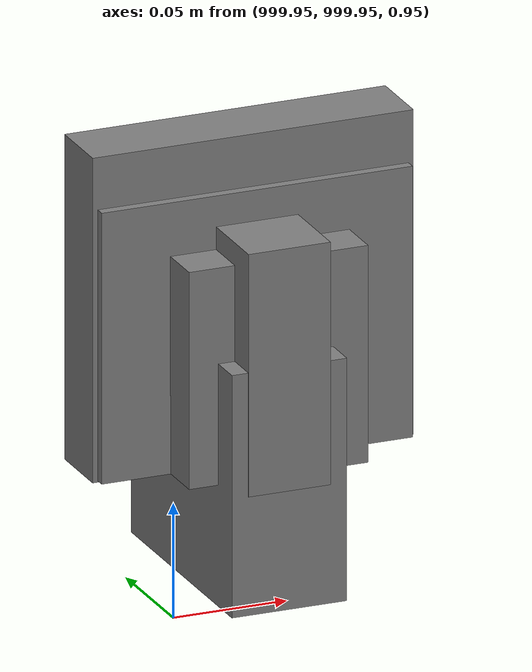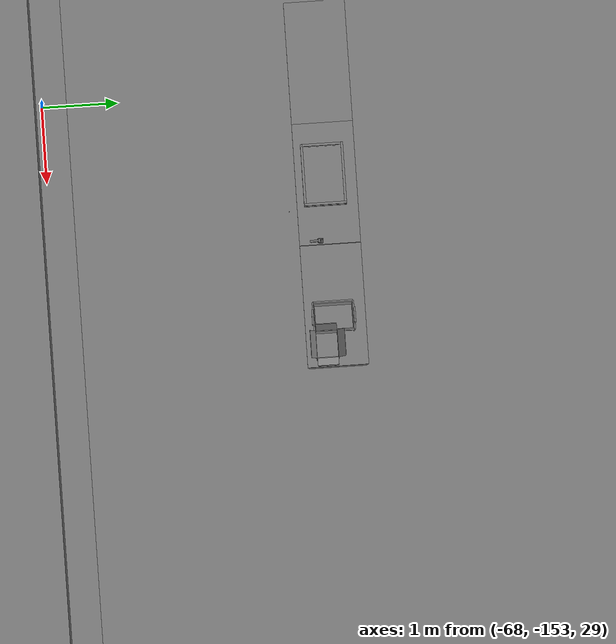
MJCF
<mujoco>
    <option gravity="0.000000000 0.000000000 -9.810000420" timestep="0.0049999999" integrator="implicitfast" density="1.225" viscosity="1.8000001e-05" noslip_iterations="10" iterations="100" sdf_iterations="50">
        <flag multiccd="disable"/>
    </option>
    <size memory="1000M"/>
    <compiler coordinate="local"/>
    <worldbody>
        <light cutoff="30" pos="0 1 1" dir="0 -1 -2"/>
        <light cutoff="30" pos="0 -1 1" dir="0 1 -2"/>
        <body pos="-66.045280457 -148.929275513 31.164234161" euler="104.223159790 -3.316368818 -16.484533310" mocap="true" name="spotlight3_SpotLight"/>
        <body pos="1000.000000000 1000.000000000 1.000000000" euler="0.000000000 0.000000000 180.000000000" name="openloong_gripper_2f85_fix_base_usda_battery_01">
            <geom contype="1" conaffinity="1" density="1000" type="box" material="" rgba="0.500000000 0.500000000 0.500000000 1.000000000" solimp="0.899999976 0.949999988 0.001000000" friction="1.000000000 0.005000000 0.000100000" solref="0.020000000 1.000000000" margin="0" condim="3" group="0" pos="-0.011123657 -0.041940309 0.101691343" quat="1.000000000 0.000000000 0.000000000 0.000000000" size="0.010800000 0.003375000 0.004725000" name="openloong_gripper_2f85_fix_base_usda_geom_2D80EA7A_4616_4391_B53E_17F9FF478ADD"/>
            <geom contype="1" conaffinity="1" density="1000" type="box" material="" rgba="0.500000000 0.500000000 0.500000000 1.000000000" solimp="0.899999976 0.949999988 0.001000000" friction="1.000000000 0.005000000 0.000100000" solref="0.020000000 1.000000000" margin="0" condim="3" group="0" pos="-0.010876465 -0.044247437 0.047066893" quat="0.998702705 -0.050920475 0.000000000 0.000000000" size="0.009450001 0.002700000 0.024975000" name="openloong_gripper_2f85_fix_base_usda_geom_0D51354B_9E4F_48F3_861E_4656CA55729A"/>
            <geom contype="1" conaffinity="1" density="1000" type="box" material="" rgba="0.500000000 0.500000000 0.500000000 1.000000000" solimp="0.899999976 0.949999988 0.001000000" friction="1.000000000 0.005000000 0.000100000" solref="0.020000000 1.000000000" margin="0" condim="3" group="0" pos="-0.001235962 -0.000659180 0.047381196" quat="1.000000000 0.000000000 0.000000000 0.000000000" size="0.039420001 0.039150000 0.047250003" name="openloong_gripper_2f85_fix_base_usda_geom_AB61A0C0_7DCF_4F8D_A975_466EC9232275"/>
            <geom contype="1" conaffinity="1" density="1000" type="box" material="" rgba="0.500000000 0.500000000 0.500000000 1.000000000" solimp="0.899999976 0.949999988 0.001000000" friction="1.000000000 0.005000000 0.000100000" solref="0.020000000 1.000000000" margin="0" condim="3" group="0" pos="-0.010876465 -0.039138794 0.009851727" quat="1.000000000 0.000000000 0.000000000 0.000000000" size="0.009450001 0.010800000 0.013500000" name="openloong_gripper_2f85_fix_base_usda_geom_CAF4A15C_2D1A_4644_9254_C7C417286629"/>
            <geom contype="1" conaffinity="1" density="1000" type="box" material="" rgba="0.500000000 0.500000000 0.500000000 1.000000000" solimp="0.899999976 0.949999988 0.001000000" friction="1.000000000 0.005000000 0.000100000" solref="0.020000000 1.000000000" margin="0" condim="3" group="0" pos="-0.010876465 -0.041528322 0.071508206" quat="1.000000000 0.000000000 0.000000000 0.000000000" size="0.009450001 0.002700000 0.027000001" name="openloong_gripper_2f85_fix_base_usda_geom_59F2C619_DD89_45AF_82AC_230EF4132112"/>
            <freejoint name="openloong_gripper_2f85_fix_base_usda_battery_01_joint"/>
            <site size="0.005000000 0.005000000 0.005000000" rgba="0.500000000 0.500000000 0.500000000 1.000000000" pos="0.000000000 0.000000000 0.000000000" quat="0.999961913 0.008726500 0.000000000 0.000000000" group="0" type="sphere" name="openloong_gripper_2f85_fix_base_usda_battery_01site"/>
        </body>
        <body pos="1000.000000000 1000.000000000 1.000000000" euler="0.000000000 0.000000000 180.000000000" name="openloong_gripper_2f85_fix_base_usda_wifi_box">
            <geom contype="1" conaffinity="1" density="1000" type="box" material="" rgba="0.500000000 0.500000000 0.500000000 1.000000000" solimp="0.899999976 0.949999988 0.001000000" friction="1.000000000 0.005000000 0.000100000" solref="0.020000000 1.000000000" margin="0" condim="3" group="0" pos="0.000000000 0.000000000 0.058978677" quat="0.000000000 0.000000047 0.000000000 1.000000000" size="0.068499997 0.018999999 0.059000000" name="openloong_gripper_2f85_fix_base_usda_geom_F43B66A8_731A_4B02_8F64_C387ACBFF07F"/>
            <freejoint name="openloong_gripper_2f85_fix_base_usda_wifi_box_joint"/>
            <site size="0.005000000 0.005000000 0.005000000" rgba="0.500000000 0.500000000 0.500000000 1.000000000" pos="0.000000000 0.000000000 0.000000000" quat="0.999961913 0.008726500 0.000000000 0.000000000" group="0" type="sphere" name="openloong_gripper_2f85_fix_base_usda_wifi_boxsite"/>
        </body>
        <body pos="1000.000000000 1000.000000000 1.000000000" euler="0.000000000 0.000000000 180.000000000" name="openloong_gripper_2f85_fix_base_usda_cpu_fan">
            <geom contype="1" conaffinity="1" density="1000" type="box" material="" rgba="0.500000000 0.500000000 0.500000000 1.000000000" solimp="0.899999976 0.949999988 0.001000000" friction="1.000000000 0.005000000 0.000100000" solref="0.020000000 1.000000000" margin="0" condim="3" group="0" pos="0.000000000 0.000000000 0.070034981" quat="0.000000000 0.000000000 0.000000000 1.000000000" size="0.070700005 0.014699999 0.070700005" name="openloong_gripper_2f85_fix_base_usda_geom_804A0A6C_FC00_4F86_9371_4E326D0C2938"/>
            <freejoint name="openloong_gripper_2f85_fix_base_usda_cpu_fan_joint"/>
            <site size="0.005000000 0.005000000 0.005000000" rgba="0.500000000 0.500000000 0.500000000 1.000000000" pos="0.000000000 0.000000000 0.000000000" quat="0.999961913 0.008726535 0.000000000 0.000000000" group="0" type="sphere" name="openloong_gripper_2f85_fix_base_usda_cpu_fancsite"/>
        </body>
        <body pos="-65.931251526 -149.359481812 31.171564102" euler="20.407405853 -27.753322601 -29.080574036" mocap="true" name="spotlight6_SpotLight"/>
        <body pos="1000.000000000 1000.000000000 1.000000000" euler="0.000011953 0.000005123 -179.999984741" name="openloong_gripper_2f85_fix_base_usda_intel_box">
            <geom contype="1" conaffinity="1" density="1000" type="box" material="" rgba="0.500000000 0.500000000 0.500000000 1.000000000" solimp="0.899999976 0.949999988 0.001000000" friction="1.000000000 0.005000000 0.000100000" solref="0.020000000 1.000000000" margin="0" condim="3" group="0" pos="0.000000000 -0.000067139 0.000082284" quat="0.707106709 0.000000225 0.000000253 0.707106650" size="0.052800003 0.025300000 0.052800003" name="openloong_gripper_2f85_fix_base_usda_geom_1866DEE8_5A70_45D7_8EDD_D9D42AC153E9"/>
            <freejoint name="openloong_gripper_2f85_fix_base_usda_intel_box_joint"/>
            <site size="0.005000000 0.005000000 0.005000000" rgba="0.500000000 0.500000000 0.500000000 1.000000000" pos="0.000000000 0.000000000 0.000000000" quat="0.999961913 0.008726500 0.000000000 0.000000000" group="0" type="sphere" name="openloong_gripper_2f85_fix_base_usda_intel_boxsite"/>
        </body>
        <body pos="-66.029685974 -148.973464966 31.170646667" euler="86.243713379 -27.264802933 -106.100830078" mocap="true" name="spotlight5_SpotLight"/>
        <body pos="1000.000000000 999.999938965 1.000000000" euler="0.000000000 0.000000000 180.000000000" name="openloong_gripper_2f85_fix_base_usda_intelcore_i5">
            <geom contype="1" conaffinity="1" density="1000" type="box" material="" rgba="0.500000000 0.500000000 0.500000000 1.000000000" solimp="0.899999976 0.949999988 0.001000000" friction="1.000000000 0.005000000 0.000100000" solref="0.020000000 1.000000000" margin="0" condim="3" group="0" pos="0.000000000 0.000000000 0.051722717" quat="0.707106709 0.000000000 0.000000000 -0.707106769" size="0.052800000 0.018080002 0.052800000" name="openloong_gripper_2f85_fix_base_usda_geom_0B278C3B_C4DA_42D3_9333_051F2ECA89DC"/>
            <freejoint name="openloong_gripper_2f85_fix_base_usda_intelcore_i5_joint"/>
            <site size="0.005000000 0.005000000 0.005000000" rgba="0.500000000 0.500000000 0.500000000 1.000000000" pos="0.000000000 0.000000000 0.000000000" quat="0.999961913 0.008726534 0.000000000 0.000000000" group="0" type="sphere" name="openloong_gripper_2f85_fix_base_usda_intelcore_i5site"/>
        </body>
        <body pos="-64.866622925 -149.383972168 30.183746338" euler="89.999984741 89.999946594 0.000000000" name="openloong_gripper_2f85_fix_base_usda_bluebox_01">
            <geom contype="1" conaffinity="1" density="1000" type="box" material="" rgba="0.500000000 0.500000000 0.500000000 1.000000000" solimp="0.899999976 0.949999988 0.001000000" friction="1.000000000 0.005000000 0.000100000" solref="0.020000000 1.000000000" margin="0" condim="3" group="0" pos="0.276580811 0.187225342 0.000068665" quat="0.707106948 0.000077471 0.707106352 0.000077486" size="0.100000001 0.057999998 0.010000000" name="openloong_gripper_2f85_fix_base_usda_geom_F04FCF54_D556_4850_8985_83CC66919728"/>
            <geom contype="1" conaffinity="1" density="1000" type="box" material="" rgba="0.500000000 0.500000000 0.500000000 1.000000000" solimp="0.899999976 0.949999988 0.001000000" friction="1.000000000 0.005000000 0.000100000" solref="0.020000000 1.000000000" margin="0" condim="3" group="0" pos="0.000000000 0.002883911 0.000000000" quat="0.999999881 0.000000000 0.000000000 0.000000000" size="0.254000008 0.003000000 0.172000006" name="openloong_gripper_2f85_fix_base_usda_geom_B6969D51_6745_4546_A95A_40CB0489DFB1"/>
            <geom contype="1" conaffinity="1" density="1000" type="box" material="" rgba="0.500000000 0.500000000 0.500000000 1.000000000" solimp="0.899999976 0.949999988 0.001000000" friction="1.000000000 0.005000000 0.000100000" solref="0.020000000 1.000000000" margin="0" condim="3" group="0" pos="0.000000000 0.124874115 0.173484802" quat="0.999796331 0.020176515 -0.000000015 0.000000030" size="0.259999990 0.119999997 0.007000000" name="openloong_gripper_2f85_fix_base_usda_geom_E1C0320F_FC5F_4369_B094_CD09075C978E"/>
            <geom contype="1" conaffinity="1" density="1000" type="box" material="" rgba="0.500000000 0.500000000 0.500000000 1.000000000" solimp="0.899999976 0.949999988 0.001000000" friction="1.000000000 0.005000000 0.000100000" solref="0.020000000 1.000000000" margin="0" condim="3" group="0" pos="0.000000000 0.124874115 -0.173469543" quat="0.999796331 -0.020176545 -0.000000015 0.000000000" size="0.259999990 0.119999997 0.007000000" name="openloong_gripper_2f85_fix_base_usda_geom_1A8072A2_DE8B_4096_97E1_2C2724FFECFB"/>
            <geom contype="1" conaffinity="1" density="1000" type="box" material="" rgba="0.500000000 0.500000000 0.500000000 1.000000000" solimp="0.899999976 0.949999988 0.001000000" friction="1.000000000 0.005000000 0.000100000" solref="0.020000000 1.000000000" margin="0" condim="3" group="0" pos="0.000000000 0.214008331 0.188980103" quat="0.999912977 0.013176724 0.000000015 0.000000000" size="0.259999990 0.029999999 0.012500000" name="openloong_gripper_2f85_fix_base_usda_geom_F4C706A4_9CBF_4B29_AFFD_A92042492B5E"/>
            <geom contype="1" conaffinity="1" density="1000" type="box" material="" rgba="0.500000000 0.500000000 0.500000000 1.000000000" solimp="0.899999976 0.949999988 0.001000000" friction="1.000000000 0.005000000 0.000100000" solref="0.020000000 1.000000000" margin="0" condim="3" group="0" pos="-0.258361816 0.125289917 0.001876831" quat="0.702796936 -0.020792112 0.710783124 0.020769298" size="0.189999998 0.119999997 0.009000000" name="openloong_gripper_2f85_fix_base_usda_geom_D5789E10_5C82_4237_ADF7_3FC01A56A575"/>
            <geom contype="1" conaffinity="1" density="1000" type="box" material="" rgba="0.500000000 0.500000000 0.500000000 1.000000000" solimp="0.899999976 0.949999988 0.001000000" friction="1.000000000 0.005000000 0.000100000" solref="0.020000000 1.000000000" margin="0" condim="3" group="0" pos="0.000000000 0.214008331 -0.188980103" quat="0.999912977 -0.013176769 0.000000030 0.000000015" size="0.259999990 0.029999999 0.012500000" name="openloong_gripper_2f85_fix_base_usda_geom_BE3CC7E4_F678_42A4_BA50_4D8E358300BC"/>
            <geom contype="1" conaffinity="1" density="1000" type="box" material="" rgba="0.500000000 0.500000000 0.500000000 1.000000000" solimp="0.899999976 0.949999988 0.001000000" friction="1.000000000 0.005000000 0.000100000" solref="0.020000000 1.000000000" margin="0" condim="3" group="0" pos="-0.276611328 0.187225342 0.000068665" quat="0.707106650 0.000077441 0.707106709 0.000077456" size="0.100000001 0.057999998 0.010000000" name="openloong_gripper_2f85_fix_base_usda_geom_E875CC6F_6830_4D00_AE9D_2951B54F1C34"/>
            <geom contype="1" conaffinity="1" density="1000" type="box" material="" rgba="0.500000000 0.500000000 0.500000000 1.000000000" solimp="0.899999976 0.949999988 0.001000000" friction="1.000000000 0.005000000 0.000100000" solref="0.020000000 1.000000000" margin="0" condim="3" group="0" pos="0.258331299 0.125289917 0.001876831" quat="0.702851415 0.018856421 0.710823774 -0.019329369" size="0.189999998 0.119999997 0.009000000" name="openloong_gripper_2f85_fix_base_usda_geom_D9CE724F_D396_4E95_A96F_996F020D780D"/>
            <freejoint name="openloong_gripper_2f85_fix_base_usda_bluebox_01_joint"/>
            <site size="0.005000000 0.005000000 0.005000000" rgba="0.500000000 0.500000000 0.500000000 1.000000000" pos="0.000000000 0.000000000 0.000000000" quat="0.999961913 0.008726534 0.000000000 0.000000000" group="0" type="sphere" name="openloong_gripper_2f85_fix_base_usda_bluebox_01site"/>
        </body>
        <body pos="-64.496299744 -149.491867065 30.235729218" euler="0.000000000 0.000000000 89.999946594" name="openloong_gripper_2f85_fix_base_usda_cardboardbox_01">
            <geom contype="1" conaffinity="1" density="1000" type="box" material="" rgba="0.500000000 0.500000000 0.500000000 1.000000000" solimp="0.899999976 0.949999988 0.001000000" friction="1.000000000 0.005000000 0.000100000" solref="0.020000000 1.000000000" margin="0" condim="3" group="0" pos="-0.003166199 -0.004086494 0.005052090" quat="1.000000000 0.000000000 0.000000000 0.000000000" size="0.142499998 0.177500010 0.005000000" name="openloong_gripper_2f85_fix_base_usda_geom_53B2A90A_8B20_4B50_8C21_3EFD93D4CEAE"/>
            <geom contype="1" conaffinity="1" density="1000" type="box" material="" rgba="0.500000000 0.500000000 0.500000000 1.000000000" solimp="0.899999976 0.949999988 0.001000000" friction="1.000000000 0.005000000 0.000100000" solref="0.020000000 1.000000000" margin="0" condim="3" group="0" pos="-0.003166199 0.170316696 0.150570869" quat="1.000000000 0.000000000 0.000000000 0.000000000" size="0.142499998 0.005000000 0.149999991" name="openloong_gripper_2f85_fix_base_usda_geom_22AB4AB6_4E90_4390_86FF_8B89FB8C54C7"/>
            <geom contype="1" conaffinity="1" density="1000" type="box" material="" rgba="0.500000000 0.500000000 0.500000000 1.000000000" solimp="0.899999976 0.949999988 0.001000000" friction="1.000000000 0.005000000 0.000100000" solref="0.020000000 1.000000000" margin="0" condim="3" group="0" pos="-0.147399902 -0.005307198 0.150570869" quat="1.000000000 0.000000000 0.000000000 0.000000000" size="0.005000000 0.177500010 0.149999991" name="openloong_gripper_2f85_fix_base_usda_geom_1E8C5640_2474_4951_ABC7_00A0912E098F"/>
            <geom contype="1" conaffinity="1" density="1000" type="box" material="" rgba="0.500000000 0.500000000 0.500000000 1.000000000" solimp="0.899999976 0.949999988 0.001000000" friction="1.000000000 0.005000000 0.000100000" solref="0.020000000 1.000000000" margin="0" condim="3" group="0" pos="0.140275955 -0.005307198 0.150570869" quat="1.000000000 0.000000000 0.000000000 0.000000000" size="0.005000000 0.177500010 0.149999991" name="openloong_gripper_2f85_fix_base_usda_geom_F06D5F4A_A75B_4E8B_A9D6_FFA28CC196B8"/>
            <geom contype="1" conaffinity="1" density="1000" type="box" material="" rgba="0.500000000 0.500000000 0.500000000 1.000000000" solimp="0.899999976 0.949999988 0.001000000" friction="1.000000000 0.005000000 0.000100000" solref="0.020000000 1.000000000" margin="0" condim="3" group="0" pos="-0.003166199 -0.181550980 0.150570869" quat="1.000000000 0.000000000 0.000000000 0.000000000" size="0.142499998 0.005000000 0.149999991" name="openloong_gripper_2f85_fix_base_usda_geom_307562DC_739D_43C0_891E_022813B028A1"/>
            <freejoint name="openloong_gripper_2f85_fix_base_usda_cardboardbox_01_joint"/>
            <site size="0.005000000 0.005000000 0.005000000" rgba="0.500000000 0.500000000 0.500000000 1.000000000" pos="0.000000000 0.000000000 0.000000000" quat="0.999961913 0.008726535 0.000000000 0.000000000" group="0" type="sphere" name="openloong_gripper_2f85_fix_base_usda_site_2E7F2E5A_845B_48E8_B879_E59175185715"/>
            <body pos="0.139160156 -0.004048347 0.301930904" euler="-179.999954224 49.383502960 179.999954224" name="openloong_gripper_2f85_fix_base_usda_A1_006">
                <geom contype="1" conaffinity="1" density="1000" type="box" material="" rgba="0.500000000 0.500000000 0.500000000 1.000000000" solimp="0.899999976 0.949999988 0.001000000" friction="1.000000000 0.005000000 0.000100000" solref="0.020000000 1.000000000" margin="0" condim="3" group="0" pos="-0.071587563 0.000009537 0.001745224" quat="0.999999881 0.000000000 0.000000000 0.000000000" size="0.071249999 0.179999992 0.002500000" name="openloong_gripper_2f85_fix_base_usda_geom_C563E017_819B_4C90_95F8_AD95C57A1946"/>
                <joint armature="0" stiffness="0.07" damping="0.0099999998" axis="0.000000 1.000000 0.000000" type="hinge" name="openloong_gripper_2f85_fix_base_usda_A1_006"/>
            </body>
            <body pos="-0.145902634 -0.004086494 0.301938057" euler="-180.000000000 -60.000011444 -180.000000000" name="openloong_gripper_2f85_fix_base_usda_A2_006">
                <geom contype="1" conaffinity="1" density="1000" type="box" material="" rgba="0.500000000 0.500000000 0.500000000 1.000000000" solimp="0.899999976 0.949999988 0.001000000" friction="1.000000000 0.005000000 0.000100000" solref="0.020000000 1.000000000" margin="0" condim="3" group="0" pos="0.071268082 0.000009537 0.002717972" quat="0.000002921 0.000000000 -0.000000030 0.999999881" size="0.071249999 0.179999992 0.002500000" name="openloong_gripper_2f85_fix_base_usda_geom_DEE4CF6A_7C61_492A_B516_A53499814A28"/>
                <joint armature="0" stiffness="0.07" damping="0.0099999998" axis="0.000000 1.000000 0.000000" type="hinge" name="openloong_gripper_2f85_fix_base_usda_A2_006"/>
            </body>
            <body pos="-0.003385544 0.175991058 0.301930904" euler="-125.858116150 -0.000004561 0.000002331" name="openloong_gripper_2f85_fix_base_usda_B2_006">
                <geom contype="1" conaffinity="1" density="1000" type="box" material="" rgba="0.500000000 0.500000000 0.500000000 1.000000000" solimp="0.899999976 0.949999988 0.001000000" friction="1.000000000 0.005000000 0.000100000" solref="0.020000000 1.000000000" margin="0" condim="3" group="0" pos="0.000009537 -0.070939064 -0.002470016" quat="0.999614120 0.027776197 -0.000000015 0.000000030" size="0.137500003 0.064999998 0.005000000" name="openloong_gripper_2f85_fix_base_usda_geom_D4066DF8_2699_438B_8D39_F0C8B1A40DFF"/>
                <joint armature="0" stiffness="0.07" damping="0.0099999998" axis="1.000000 0.000000 0.000000" type="hinge" name="openloong_gripper_2f85_fix_base_usda_B2_006"/>
            </body>
            <body pos="-0.003385544 -0.184140205 0.301938057" euler="147.805557251 0.000000000 0.000000000" name="openloong_gripper_2f85_fix_base_usda_B1_006">
                <geom contype="1" conaffinity="1" density="1000" type="box" material="" rgba="0.500000000 0.500000000 0.500000000 1.000000000" solimp="0.899999976 0.949999988 0.001000000" friction="1.000000000 0.005000000 0.000100000" solref="0.020000000 1.000000000" margin="0" condim="3" group="0" pos="-0.000028610 0.070202351 -0.002703667" quat="0.999614179 -0.027776167 0.000000000 0.000000000" size="0.137500003 0.064999998 0.005000000" name="openloong_gripper_2f85_fix_base_usda_geom_F2466146_C96D_40FC_88BA_BA0B46C9C2F5"/>
                <joint armature="0" stiffness="0.07" damping="0.0099999998" axis="1.000000 0.000000 0.000000" type="hinge" name="openloong_gripper_2f85_fix_base_usda_B1_006"/>
            </body>
        </body>
        <body pos="-65.882858276 -149.481979370 30.229999542" euler="-64.487716675 0.000000000 0.000000000" name="openloong_gripper_2f85_fix_base_usda_Barcode">
            <geom contype="1" conaffinity="1" density="1000" type="box" material="" rgba="0.500000000 0.500000000 0.500000000 1.000000000" solimp="0.899999976 0.949999988 0.001000000" friction="1.000000000 0.005000000 0.000100000" solref="0.020000000 1.000000000" margin="0" condim="3" group="0" pos="0.000000000 0.013038635 0.001419067" quat="0.000000000 0.000000000 0.000000000 1.000000119" size="0.034000002 0.010000000 0.017999999" name="openloong_gripper_2f85_fix_base_usda_geom_AF4AFDB9_10EF_4F19_B42F_CEADC03C5AE4"/>
            <geom contype="1" conaffinity="1" density="1000" type="box" material="" rgba="0.500000000 0.500000000 0.500000000 1.000000000" solimp="0.899999976 0.949999988 0.001000000" friction="1.000000000 0.005000000 0.000100000" solref="0.020000000 1.000000000" margin="0" condim="3" group="0" pos="0.000000000 -0.035301208 -0.007095337" quat="0.000000000 0.000000000 -0.043619365 0.999048233" size="0.028999999 0.010000000 0.020000000" name="openloong_gripper_2f85_fix_base_usda_geom_DAF8F1A6_BDD3_4788_AD36_9083AB4CDE0E"/>
            <geom contype="1" conaffinity="1" density="1000" type="box" material="" rgba="0.500000000 0.500000000 0.500000000 1.000000000" solimp="0.899999976 0.949999988 0.001000000" friction="1.000000000 0.005000000 0.000100000" solref="0.020000000 1.000000000" margin="0" condim="3" group="0" pos="0.000000000 -0.043411255 -0.011749268" quat="0.922262907 0.386563420 0.000000000 0.000000000" size="0.026000001 0.010000000 0.020000000" name="openloong_gripper_2f85_fix_base_usda_geom_33FD5B15_BB46_4156_B7AB_DF3A970B5007"/>
            <geom contype="1" conaffinity="1" density="1000" type="box" material="" rgba="0.500000000 0.500000000 0.500000000 1.000000000" solimp="0.899999976 0.949999988 0.001000000" friction="1.000000000 0.005000000 0.000100000" solref="0.020000000 1.000000000" margin="0" condim="3" group="0" pos="0.000000000 -0.016967773 -0.031860352" quat="0.000000000 0.000000000 0.000000000 1.000000119" size="0.008000000 0.010000000 0.013000000" name="openloong_gripper_2f85_fix_base_usda_geom_D192F14C_96FF_46EB_9839_FC3AAA1395ED"/>
            <geom contype="1" conaffinity="1" density="1000" type="box" material="" rgba="0.500000000 0.500000000 0.500000000 1.000000000" solimp="0.899999976 0.949999988 0.001000000" friction="1.000000000 0.005000000 0.000100000" solref="0.020000000 1.000000000" margin="0" condim="3" group="0" pos="0.000000000 -0.001869202 0.000312805" quat="0.953716993 0.300705761 0.000000000 0.000000000" size="0.032000002 0.010000000 0.018999999" name="openloong_gripper_2f85_fix_base_usda_geom_F9A905CD_993C_4629_A784_A28272D36C17"/>
            <geom contype="1" conaffinity="1" density="1000" type="box" material="" rgba="0.500000000 0.500000000 0.500000000 1.000000000" solimp="0.899999976 0.949999988 0.001000000" friction="1.000000000 0.005000000 0.000100000" solref="0.020000000 1.000000000" margin="0" condim="3" group="0" pos="0.000000000 -0.019531250 -0.003173828" quat="0.953716993 0.300705761 0.000000000 0.000000000" size="0.030999999 0.010000000 0.020000000" name="openloong_gripper_2f85_fix_base_usda_geom_F3427978_34AA_4CCC_984B_F79BA6B0EF00"/>
            <geom contype="1" conaffinity="1" density="1000" type="box" material="" rgba="0.500000000 0.500000000 0.500000000 1.000000000" solimp="0.899999976 0.949999988 0.001000000" friction="1.000000000 0.005000000 0.000100000" solref="0.020000000 1.000000000" margin="0" condim="3" group="0" pos="0.000000000 -0.035301208 -0.007095337" quat="0.953716993 0.300705761 0.000000000 0.000000000" size="0.028999999 0.010000000 0.020000000" name="openloong_gripper_2f85_fix_base_usda_geom_B583F8CB_6BA8_44E8_A312_04871D737D0E"/>
            <geom contype="1" conaffinity="1" density="1000" type="box" material="" rgba="0.500000000 0.500000000 0.500000000 1.000000000" solimp="0.899999976 0.949999988 0.001000000" friction="1.000000000 0.005000000 0.000100000" solref="0.020000000 1.000000000" margin="0" condim="3" group="0" pos="0.000000000 -0.042617798 -0.071121216" quat="0.000000000 0.000000000 0.000000000 1.000000119" size="0.013000000 0.021000000 0.059999999" name="openloong_gripper_2f85_fix_base_usda_geom_EA6A5E9E_CA27_4AAD_A926_CDEE2CFE1BA3"/>
            <freejoint name="openloong_gripper_2f85_fix_base_usda_Barcode_joint"/>
            <site size="0.005000000 0.005000000 0.005000000" rgba="0.500000000 0.500000000 0.500000000 1.000000000" pos="0.000000000 0.000000000 0.000000000" quat="1.000000000 0.000000000 0.000000000 0.000000000" group="0" type="sphere" name="openloong_gripper_2f85_fix_base_usda_Barcode_site"/>
        </body>
        <body pos="-66.745018005 -149.392349243 30.184000015" euler="0.000000000 0.000000000 89.999946594" name="[22331197244658]_Basket_01">
            <geom contype="1" conaffinity="1" density="1000" type="box" material="" rgba="0.500000000 0.500000000 0.500000000 1.000000000" solimp="0.899999976 0.949999988 0.001000000" friction="1.000000000 0.005000000 0.000100000" solref="0.020000000 1.000000000" margin="0" condim="3" group="0" pos="-0.052425385 0.389207840 0.089787483" quat="0.707107008 0.000000000 0.000000000 0.707106411" size="0.014249999 0.014249999 0.059999999" name="[22331197244658]_geom_278D63E9_747F_4874_8EE3_00B1ECC8EFB7"/>
            <geom contype="1" conaffinity="1" density="1000" type="box" material="" rgba="0.500000000 0.500000000 0.500000000 1.000000000" solimp="0.899999976 0.949999988 0.001000000" friction="1.000000000 0.005000000 0.000100000" solref="0.020000000 1.000000000" margin="0" condim="3" group="0" pos="0.264015198 -0.133043289 0.089787483" quat="0.707107008 0.000000000 0.000000000 0.707106411" size="0.014249999 0.014249999 0.059999999" name="[22331197244658]_geom_45F7DBDF_81EC_4C77_8421_C52D2E294FF6"/>
            <geom contype="1" conaffinity="1" density="1000" type="box" material="" rgba="0.500000000 0.500000000 0.500000000 1.000000000" solimp="0.899999976 0.949999988 0.001000000" friction="1.000000000 0.005000000 0.000100000" solref="0.020000000 1.000000000" margin="0" condim="3" group="0" pos="-0.264015198 -0.265548706 0.089793205" quat="0.707107008 0.000000000 0.000000000 0.707106411" size="0.014249999 0.014249999 0.059999999" name="[22331197244658]_geom_EA231144_AD21_4C00_908A_D13F351B49CA"/>
            <geom contype="1" conaffinity="1" density="1000" type="box" material="" rgba="0.500000000 0.500000000 0.500000000 1.000000000" solimp="0.899999976 0.949999988 0.001000000" friction="1.000000000 0.005000000 0.000100000" solref="0.020000000 1.000000000" margin="0" condim="3" group="0" pos="-0.160263062 -0.389322281 0.089793205" quat="0.707107008 0.000000000 0.000000000 0.707106411" size="0.014249999 0.014249999 0.059999999" name="[22331197244658]_geom_FDBE85B0_0127_40C9_AE30_673546C31579"/>
            <geom contype="1" conaffinity="1" density="1000" type="box" material="" rgba="0.500000000 0.500000000 0.500000000 1.000000000" solimp="0.899999976 0.949999988 0.001000000" friction="1.000000000 0.005000000 0.000100000" solref="0.020000000 1.000000000" margin="0" condim="3" group="0" pos="0.162265778 -0.389322281 0.089787483" quat="0.707107008 0.000000000 0.000000000 0.707106411" size="0.014249999 0.014249999 0.059999999" name="[22331197244658]_geom_BE9C9D98_1EB9_4669_BA71_1D629327D046"/>
            <geom contype="1" conaffinity="1" density="1000" type="box" material="" rgba="0.500000000 0.500000000 0.500000000 1.000000000" solimp="0.899999976 0.949999988 0.001000000" friction="1.000000000 0.005000000 0.000100000" solref="0.020000000 1.000000000" margin="0" condim="3" group="0" pos="0.264015198 0.389207840 0.089787483" quat="0.707107008 0.000000000 0.000000000 0.707106411" size="0.014249999 0.014249999 0.059999999" name="[22331197244658]_geom_BD73F1A6_0B43_4851_86B8_46A51EA4A48F"/>
            <geom contype="1" conaffinity="1" density="1000" type="box" material="" rgba="0.500000000 0.500000000 0.500000000 1.000000000" solimp="0.899999976 0.949999988 0.001000000" friction="1.000000000 0.005000000 0.000100000" solref="0.020000000 1.000000000" margin="0" condim="3" group="0" pos="-0.264015198 -0.133043289 0.089793205" quat="0.707107008 0.000000000 0.000000000 0.707106411" size="0.014249999 0.014249999 0.059999999" name="[22331197244658]_geom_E3E45C24_4FB7_4F0A_B9CC_70841CBA35A3"/>
            <geom contype="1" conaffinity="1" density="1000" type="box" material="" rgba="0.500000000 0.500000000 0.500000000 1.000000000" solimp="0.899999976 0.949999988 0.001000000" friction="1.000000000 0.005000000 0.000100000" solref="0.020000000 1.000000000" margin="0" condim="3" group="0" pos="-0.264026642 0.269256592 0.089793205" quat="0.707107008 0.000000000 0.000000000 0.707106411" size="0.014249999 0.014249999 0.059999999" name="[22331197244658]_geom_66947F2B_4FF6_4504_88D4_3ED8F8F6C033"/>
            <geom contype="1" conaffinity="1" density="1000" type="box" material="" rgba="0.500000000 0.500000000 0.500000000 1.000000000" solimp="0.899999976 0.949999988 0.001000000" friction="1.000000000 0.005000000 0.000100000" solref="0.020000000 1.000000000" margin="0" condim="3" group="0" pos="0.054462433 0.389207840 0.089787483" quat="0.707107008 0.000000000 0.000000000 0.707106411" size="0.014249999 0.014249999 0.059999999" name="[22331197244658]_geom_E9043AE5_0D20_46A9_A714_EBC2403A1C27"/>
            <geom contype="1" conaffinity="1" density="1000" type="box" material="" rgba="0.500000000 0.500000000 0.500000000 1.000000000" solimp="0.899999976 0.949999988 0.001000000" friction="1.000000000 0.005000000 0.000100000" solref="0.020000000 1.000000000" margin="0" condim="3" group="0" pos="0.054462433 -0.389322281 0.089787483" quat="0.707107008 0.000000000 0.000000000 0.707106411" size="0.014249999 0.014249999 0.059999999" name="[22331197244658]_geom_6BE833B9_43E5_49A8_836E_7200C60A8ABF"/>
            <geom contype="1" conaffinity="1" density="1000" type="box" material="" rgba="0.500000000 0.500000000 0.500000000 1.000000000" solimp="0.899999976 0.949999988 0.001000000" friction="1.000000000 0.005000000 0.000100000" solref="0.020000000 1.000000000" margin="0" condim="3" group="0" pos="0.264015198 0.269256592 0.089793205" quat="0.707107008 0.000000000 0.000000000 0.707106411" size="0.014249999 0.014249999 0.059999999" name="[22331197244658]_geom_22FC5230_A356_4E86_B30F_35793A7435C0"/>
            <geom contype="1" conaffinity="1" density="1000" type="box" material="" rgba="0.500000000 0.500000000 0.500000000 1.000000000" solimp="0.899999976 0.949999988 0.001000000" friction="1.000000000 0.005000000 0.000100000" solref="0.020000000 1.000000000" margin="0" condim="3" group="0" pos="0.264015198 -0.389322281 0.089787483" quat="0.707107008 0.000000000 0.000000000 0.707106411" size="0.014249999 0.014249999 0.059999999" name="[22331197244658]_geom_54904104_0EAA_47B9_A64D_4899EF908243"/>
            <geom contype="1" conaffinity="1" density="1000" type="box" material="" rgba="0.500000000 0.500000000 0.500000000 1.000000000" solimp="0.899999976 0.949999988 0.001000000" friction="1.000000000 0.005000000 0.000100000" solref="0.020000000 1.000000000" margin="0" condim="3" group="0" pos="0.000000000 0.000000000 0.015998840" quat="0.707107008 0.000000000 0.000000000 0.707106411" size="0.403499991 0.279000014 0.015750000" name="[22331197244658]_geom_29D6BD8A_0257_44EE_A7E2_2B0DE3112B38"/>
            <geom contype="1" conaffinity="1" density="1000" type="box" material="" rgba="0.500000000 0.500000000 0.500000000 1.000000000" solimp="0.899999976 0.949999988 0.001000000" friction="1.000000000 0.005000000 0.000100000" solref="0.020000000 1.000000000" margin="0" condim="3" group="0" pos="0.000000000 -0.389476776 0.163619041" quat="0.707107008 0.000000000 0.000000000 0.707106411" size="0.015000000 0.277500004 0.015750000" name="[22331197244658]_geom_77DB96CD_4ED9_4AB0_AC6B_3DE734DDE505"/>
            <geom contype="1" conaffinity="1" density="1000" type="box" material="" rgba="0.500000000 0.500000000 0.500000000 1.000000000" solimp="0.899999976 0.949999988 0.001000000" friction="1.000000000 0.005000000 0.000100000" solref="0.020000000 1.000000000" margin="0" condim="3" group="0" pos="0.162265778 0.389207840 0.089787483" quat="0.707107008 0.000000000 0.000000000 0.707106411" size="0.014249999 0.014249999 0.059999999" name="[22331197244658]_geom_E03E7ADA_F47A_492A_BEF3_6602EF0F6410"/>
            <geom contype="1" conaffinity="1" density="1000" type="box" material="" rgba="0.500000000 0.500000000 0.500000000 1.000000000" solimp="0.899999976 0.949999988 0.001000000" friction="1.000000000 0.005000000 0.000100000" solref="0.020000000 1.000000000" margin="0" condim="3" group="0" pos="0.000000000 0.389471054 0.163619041" quat="0.707107008 0.000000000 0.000000000 0.707106411" size="0.015000000 0.277500004 0.015750000" name="[22331197244658]_geom_C17BE4F0_A24B_418E_811A_2435286C9186"/>
            <geom contype="1" conaffinity="1" density="1000" type="box" material="" rgba="0.500000000 0.500000000 0.500000000 1.000000000" solimp="0.899999976 0.949999988 0.001000000" friction="1.000000000 0.005000000 0.000100000" solref="0.020000000 1.000000000" margin="0" condim="3" group="0" pos="-0.263511658 0.000000000 0.163619041" quat="0.707107008 0.000000000 0.000000000 0.707106411" size="0.403499991 0.015000000 0.015750000" name="[22331197244658]_geom_23B8DDC3_6789_4079_856C_22CDDAEA6009"/>
            <geom contype="1" conaffinity="1" density="1000" type="box" material="" rgba="0.500000000 0.500000000 0.500000000 1.000000000" solimp="0.899999976 0.949999988 0.001000000" friction="1.000000000 0.005000000 0.000100000" solref="0.020000000 1.000000000" margin="0" condim="3" group="0" pos="-0.264015198 0.141334534 0.089793205" quat="0.707107008 0.000000000 0.000000000 0.707106411" size="0.014249999 0.014249999 0.059999999" name="[22331197244658]_geom_03675ABE_B069_4FF6_9AF1_123075E21DE8"/>
            <geom contype="1" conaffinity="1" density="1000" type="box" material="" rgba="0.500000000 0.500000000 0.500000000 1.000000000" solimp="0.899999976 0.949999988 0.001000000" friction="1.000000000 0.005000000 0.000100000" solref="0.020000000 1.000000000" margin="0" condim="3" group="0" pos="0.264015198 -0.265548706 0.089787483" quat="0.707107008 0.000000000 0.000000000 0.707106411" size="0.014249999 0.014249999 0.059999999" name="[22331197244658]_geom_2F803289_C777_476A_B54A_ED1C4A74E410"/>
            <geom contype="1" conaffinity="1" density="1000" type="box" material="" rgba="0.500000000 0.500000000 0.500000000 1.000000000" solimp="0.899999976 0.949999988 0.001000000" friction="1.000000000 0.005000000 0.000100000" solref="0.020000000 1.000000000" margin="0" condim="3" group="0" pos="-0.160263062 0.389207840 0.089787483" quat="0.707107008 0.000000000 0.000000000 0.707106411" size="0.014249999 0.014249999 0.059999999" name="[22331197244658]_geom_486268E4_38A6_4A75_B0AE_F0418607E1BC"/>
            <geom contype="1" conaffinity="1" density="1000" type="box" material="" rgba="0.500000000 0.500000000 0.500000000 1.000000000" solimp="0.899999976 0.949999988 0.001000000" friction="1.000000000 0.005000000 0.000100000" solref="0.020000000 1.000000000" margin="0" condim="3" group="0" pos="-0.052425385 -0.389322281 0.089787483" quat="0.707107008 0.000000000 0.000000000 0.707106411" size="0.014249999 0.014249999 0.059999999" name="[22331197244658]_geom_F1550194_FE18_4023_B423_EDA167037462"/>
            <geom contype="1" conaffinity="1" density="1000" type="box" material="" rgba="0.500000000 0.500000000 0.500000000 1.000000000" solimp="0.899999976 0.949999988 0.001000000" friction="1.000000000 0.005000000 0.000100000" solref="0.020000000 1.000000000" margin="0" condim="3" group="0" pos="-0.264026642 -0.389322281 0.089793205" quat="0.707107008 0.000000000 0.000000000 0.707106411" size="0.014249999 0.014249999 0.059999999" name="[22331197244658]_geom_80CE583B_B229_443E_97D6_0ADB309F2FE2"/>
            <geom contype="1" conaffinity="1" density="1000" type="box" material="" rgba="0.500000000 0.500000000 0.500000000 1.000000000" solimp="0.899999976 0.949999988 0.001000000" friction="1.000000000 0.005000000 0.000100000" solref="0.020000000 1.000000000" margin="0" condim="3" group="0" pos="0.264015198 0.141334534 0.089787483" quat="0.707107008 0.000000000 0.000000000 0.707106411" size="0.014249999 0.014249999 0.059999999" name="[22331197244658]_geom_A924D859_DC57_4166_A7A4_FCAF2D193872"/>
            <geom contype="1" conaffinity="1" density="1000" type="box" material="" rgba="0.500000000 0.500000000 0.500000000 1.000000000" solimp="0.899999976 0.949999988 0.001000000" friction="1.000000000 0.005000000 0.000100000" solref="0.020000000 1.000000000" margin="0" condim="3" group="0" pos="-0.264015198 0.389207840 0.089793205" quat="0.707107008 0.000000000 0.000000000 0.707106411" size="0.014249999 0.014249999 0.059999999" name="[22331197244658]_geom_8C93F3D4_68BF_4EDA_B322_38B457243FD3"/>
            <geom contype="1" conaffinity="1" density="1000" type="box" material="" rgba="0.500000000 0.500000000 0.500000000 1.000000000" solimp="0.899999976 0.949999988 0.001000000" friction="1.000000000 0.005000000 0.000100000" solref="0.020000000 1.000000000" margin="0" condim="3" group="0" pos="0.264015198 0.004480362 0.089787483" quat="0.707107008 0.000000000 0.000000000 0.707106411" size="0.014249999 0.014249999 0.059999999" name="[22331197244658]_geom_D75D0960_733F_4C83_987C_E00748B0C4BF"/>
            <geom contype="1" conaffinity="1" density="1000" type="box" material="" rgba="0.500000000 0.500000000 0.500000000 1.000000000" solimp="0.899999976 0.949999988 0.001000000" friction="1.000000000 0.005000000 0.000100000" solref="0.020000000 1.000000000" margin="0" condim="3" group="0" pos="0.263694763 -0.000011444 0.163619041" quat="0.707107008 0.000000000 0.000000000 0.707106411" size="0.403499991 0.015000000 0.015750000" name="[22331197244658]_geom_6C477603_3C30_4D16_9C54_1C8E9B67A3FE"/>
            <geom contype="1" conaffinity="1" density="1000" type="box" material="" rgba="0.500000000 0.500000000 0.500000000 1.000000000" solimp="0.899999976 0.949999988 0.001000000" friction="1.000000000 0.005000000 0.000100000" solref="0.020000000 1.000000000" margin="0" condim="3" group="0" pos="-0.264015198 0.004480362 0.089793205" quat="0.707107008 0.000000000 0.000000000 0.707106411" size="0.014249999 0.014249999 0.059999999" name="[22331197244658]_geom_5719F068_B2CF_4C71_977C_9E903DBEE93D"/>
            <freejoint name="[22331197244658]_joint_7076E156_BA3D_480F_929F_2921F528459B"/>
        </body>
        <body pos="0.000000000 0.000000000 0.000000000" euler="0.000000000 0.000000000 0.000000000" name="Static Objects_Static Objects">
            <geom contype="1" conaffinity="1" density="1000" type="box" material="" rgba="0.500000000 0.500000000 0.500000000 1.000000000" solimp="0.899999976 0.949999988 0.001000000" friction="1.000000000 0.005000000 0.000100000" solref="0.020000000 1.000000000" margin="0" condim="3" group="0" pos="-67.544113159 -149.365814209 29.727830887" quat="0.500000417 0.499999970 0.499999553 0.499999970" size="0.381000012 0.319999993 0.041000001" name="Static Objects_geom_74C9B8CC_094D_4952_A6BF_F76A53FD6F82"/>
            <geom contype="1" conaffinity="1" density="1000" type="box" material="" rgba="0.500000000 0.500000000 0.500000000 1.000000000" solimp="0.899999976 0.949999988 0.001000000" friction="1.000000000 0.005000000 0.000100000" solref="0.020000000 1.000000000" margin="0" condim="3" group="0" pos="-68.239501953 -149.365814209 30.086868286" quat="0.500000417 0.499999970 0.499999553 0.499999970" size="0.370999992 0.039500002 0.745000005" name="Static Objects_geom_A535BF94_7B7C_485B_AA1B_9F50B41C88C2"/>
            <geom contype="1" conaffinity="1" density="1000" type="box" material="" rgba="0.500000000 0.500000000 0.500000000 1.000000000" solimp="0.899999976 0.949999988 0.001000000" friction="1.000000000 0.005000000 0.000100000" solref="0.020000000 1.000000000" margin="0" condim="3" group="0" pos="-68.239501953 -149.365814209 30.147235870" quat="0.500000417 0.499999970 0.499999553 0.499999970" size="0.400000006 0.022000000 0.800000012" name="Static Objects_geom_5614CA30_FC99_4C63_A09C_BEF009A31059"/>
            <geom contype="1" conaffinity="1" density="1000" type="box" material="" rgba="0.500000000 0.500000000 0.500000000 1.000000000" solimp="0.899999976 0.949999988 0.001000000" friction="1.000000000 0.005000000 0.000100000" solref="0.020000000 1.000000000" margin="0" condim="3" group="0" pos="-68.934890747 -149.365814209 29.727830887" quat="0.500000417 0.499999970 0.499999553 0.499999970" size="0.381000012 0.319999993 0.041000001" name="Static Objects_geom_46C22734_F15C_4087_88CB_42E4E81F82C8"/>
            <geom contype="1" conaffinity="1" density="1000" type="box" material="" rgba="0.500000000 0.500000000 0.500000000 1.000000000" solimp="0.899999976 0.949999988 0.001000000" friction="1.000000000 0.005000000 0.000100000" solref="0.020000000 1.000000000" margin="0" condim="3" group="0" pos="-68.239501953 -149.365814209 29.561563492" quat="0.500000417 0.499999970 0.499999553 0.499999970" size="0.020000000 0.022000000 0.660000026" name="Static Objects_geom_98EB0D73_FE35_4412_84A6_E3288EF2D07E"/>
            <geom contype="1" conaffinity="1" density="1000" type="box" material="" rgba="0.500000000 0.500000000 0.500000000 1.000000000" solimp="0.899999976 0.949999988 0.001000000" friction="1.000000000 0.005000000 0.000100000" solref="0.020000000 1.000000000" margin="0" condim="3" group="0" pos="-65.945671082 -149.365814209 29.727830887" quat="0.500000417 0.499999970 0.499999553 0.499999970" size="0.381000012 0.319999993 0.041000001" name="Static Objects_geom_C878EF4F_AA3B_4756_8DA0_533FB47853AE"/>
            <geom contype="1" conaffinity="1" density="1000" type="box" material="" rgba="0.500000000 0.500000000 0.500000000 1.000000000" solimp="0.899999976 0.949999988 0.001000000" friction="1.000000000 0.005000000 0.000100000" solref="0.020000000 1.000000000" margin="0" condim="3" group="0" pos="-66.641059875 -149.365814209 30.086868286" quat="0.500000417 0.499999970 0.499999553 0.499999970" size="0.370999992 0.039500002 0.745000005" name="Static Objects_geom_60C627BF_40E4_4B92_93BC_BC813928B6FD"/>
            <geom contype="1" conaffinity="1" density="1000" type="box" material="" rgba="0.500000000 0.500000000 0.500000000 1.000000000" solimp="0.899999976 0.949999988 0.001000000" friction="1.000000000 0.005000000 0.000100000" solref="0.020000000 1.000000000" margin="0" condim="3" group="0" pos="-66.641059875 -149.365814209 30.147235870" quat="0.500000417 0.499999970 0.499999553 0.499999970" size="0.400000006 0.022000000 0.800000012" name="Static Objects_geom_6D6CF190_4736_4A3C_925B_4E6B48A0B528"/>
            <geom contype="1" conaffinity="1" density="1000" type="box" material="" rgba="0.500000000 0.500000000 0.500000000 1.000000000" solimp="0.899999976 0.949999988 0.001000000" friction="1.000000000 0.005000000 0.000100000" solref="0.020000000 1.000000000" margin="0" condim="3" group="0" pos="-67.336448669 -149.365814209 29.727830887" quat="0.500000417 0.499999970 0.499999553 0.499999970" size="0.381000012 0.319999993 0.041000001" name="Static Objects_geom_D139193E_A0B8_4136_95CA_C8F704CFB7D0"/>
            <geom contype="1" conaffinity="1" density="1000" type="box" material="" rgba="0.500000000 0.500000000 0.500000000 1.000000000" solimp="0.899999976 0.949999988 0.001000000" friction="1.000000000 0.005000000 0.000100000" solref="0.020000000 1.000000000" margin="0" condim="3" group="0" pos="-66.641059875 -149.365814209 29.561563492" quat="0.500000417 0.499999970 0.499999553 0.499999970" size="0.020000000 0.022000000 0.660000026" name="Static Objects_geom_22EB6804_589D_4358_8229_9745636896FA"/>
            <geom contype="1" conaffinity="1" density="1000" type="box" material="" rgba="0.500000000 0.500000000 0.500000000 1.000000000" solimp="0.899999976 0.949999988 0.001000000" friction="1.000000000 0.005000000 0.000100000" solref="0.020000000 1.000000000" margin="0" condim="3" group="0" pos="-64.338577271 -149.365814209 29.727830887" quat="0.500000417 0.499999970 0.499999553 0.499999970" size="0.381000012 0.319999993 0.041000001" name="Static Objects_geom_AB8B8436_B2CA_44E4_A52F_A01614A38117"/>
            <geom contype="1" conaffinity="1" density="1000" type="box" material="" rgba="0.500000000 0.500000000 0.500000000 1.000000000" solimp="0.899999976 0.949999988 0.001000000" friction="1.000000000 0.005000000 0.000100000" solref="0.020000000 1.000000000" margin="0" condim="3" group="0" pos="-65.033966064 -149.365814209 30.086868286" quat="0.500000417 0.499999970 0.499999553 0.499999970" size="0.370999992 0.039500002 0.745000005" name="Static Objects_geom_ECF66497_0D18_4927_A3E4_6ABB3A1EA33D"/>
            <geom contype="1" conaffinity="1" density="1000" type="box" material="" rgba="0.500000000 0.500000000 0.500000000 1.000000000" solimp="0.899999976 0.949999988 0.001000000" friction="1.000000000 0.005000000 0.000100000" solref="0.020000000 1.000000000" margin="0" condim="3" group="0" pos="-65.033966064 -149.365814209 30.147235870" quat="0.500000417 0.499999970 0.499999553 0.499999970" size="0.400000006 0.022000000 0.800000012" name="Static Objects_geom_364A29FD_88BB_4623_A74A_7C626DA7C4C1"/>
            <geom contype="1" conaffinity="1" density="1000" type="box" material="" rgba="0.500000000 0.500000000 0.500000000 1.000000000" solimp="0.899999976 0.949999988 0.001000000" friction="1.000000000 0.005000000 0.000100000" solref="0.020000000 1.000000000" margin="0" condim="3" group="0" pos="-65.729354858 -149.365814209 29.727830887" quat="0.500000417 0.499999970 0.499999553 0.499999970" size="0.381000012 0.319999993 0.041000001" name="Static Objects_geom_524B2FC7_B3D3_48E2_95A5_3DD315B8E48B"/>
            <geom contype="1" conaffinity="1" density="1000" type="box" material="" rgba="0.500000000 0.500000000 0.500000000 1.000000000" solimp="0.899999976 0.949999988 0.001000000" friction="1.000000000 0.005000000 0.000100000" solref="0.020000000 1.000000000" margin="0" condim="3" group="0" pos="-65.033966064 -149.365814209 29.561563492" quat="0.500000417 0.499999970 0.499999553 0.499999970" size="0.020000000 0.022000000 0.660000026" name="Static Objects_geom_20713FA2_8CE0_4FFB_B351_A44A9A43895E"/>
            <geom contype="1" conaffinity="1" density="1000" type="box" material="" rgba="0.500000000 0.500000000 0.500000000 1.000000000" solimp="0.899999976 0.949999988 0.001000000" friction="1.000000000 0.005000000 0.000100000" solref="0.020000000 1.000000000" margin="0" condim="3" group="0" pos="-61.754566193 -137.853729248 33.906845093" quat="0.707107067 0.000000000 0.000000000 0.707106471" size="0.759999990 0.759999990 4.500000000" name="Static Objects_geom_7F935581_AC39_43E8_84BB_E3BC1C0881A3"/>
            <geom contype="1" conaffinity="1" density="1000" type="box" material="" rgba="0.500000000 0.500000000 0.500000000 1.000000000" solimp="0.899999976 0.949999988 0.001000000" friction="1.000000000 0.005000000 0.000100000" solref="0.020000000 1.000000000" margin="0" condim="3" group="0" pos="-57.511135101 -144.927108765 31.707921982" quat="1.000000000 0.000000000 0.000000000 0.000000000" size="0.200000003 8.000000000 2.299999952" name="Static Objects_geom_1435EFE1_61AB_4E1F_A355_8B4180A4A8C2"/>
            <geom contype="1" conaffinity="1" density="1000" type="box" material="" rgba="0.500000000 0.500000000 0.500000000 1.000000000" solimp="0.899999976 0.949999988 0.001000000" friction="1.000000000 0.005000000 0.000100000" solref="0.020000000 1.000000000" margin="0" condim="3" group="0" pos="-80.517646790 -157.574050903 31.688196182" quat="0.707107067 0.000000000 0.000000000 0.707106471" size="0.600000024 0.600000024 2.299999952" name="Static Objects_geom_2DA6AB7D_0D6D_417D_86A3_24B09BE23C1B"/>
            <geom contype="1" conaffinity="1" density="1000" type="box" material="" rgba="0.500000000 0.500000000 0.500000000 1.000000000" solimp="0.899999976 0.949999988 0.001000000" friction="1.000000000 0.005000000 0.000100000" solref="0.020000000 1.000000000" margin="0" condim="3" group="0" pos="-80.711044312 -147.414932251 31.666158676" quat="1.000000000 0.000000000 0.000000000 0.000000000" size="0.200000003 10.000000000 2.299999952" name="Static Objects_geom_C7EEFCED_5DBA_413A_8E65_5EE977E45823"/>
            <geom contype="1" conaffinity="1" density="1000" type="box" material="" rgba="0.500000000 0.500000000 0.500000000 1.000000000" solimp="0.899999976 0.949999988 0.001000000" friction="1.000000000 0.005000000 0.000100000" solref="0.020000000 1.000000000" margin="0" condim="3" group="0" pos="-57.687217712 -137.434692383 31.688196182" quat="0.707107067 0.000000000 0.000000000 0.707106471" size="0.600000024 0.600000024 2.299999952" name="Static Objects_geom_C2C831A4_D63E_46B6_A1A3_8B2FD38AA44F"/>
            <geom contype="1" conaffinity="1" density="1000" type="box" material="" rgba="0.500000000 0.500000000 0.500000000 1.000000000" solimp="0.899999976 0.949999988 0.001000000" friction="1.000000000 0.005000000 0.000100000" solref="0.020000000 1.000000000" margin="0" condim="3" group="0" pos="-69.537033081 -140.263229370 31.714921951" quat="0.707107067 0.000000000 0.000000000 0.707106471" size="0.759999990 4.500000000 2.299999952" name="Static Objects_geom_0782D7AC_559A_4D99_AAC7_F3E5DFB0C34C"/>
            <geom contype="1" conaffinity="1" density="1000" type="box" material="" rgba="0.500000000 0.500000000 0.500000000 1.000000000" solimp="0.899999976 0.949999988 0.001000000" friction="1.000000000 0.005000000 0.000100000" solref="0.020000000 1.000000000" margin="0" condim="3" group="0" pos="-80.073638916 -137.853713989 33.906845093" quat="0.707107067 0.000000000 0.000000000 0.707106471" size="0.759999990 0.759999990 4.500000000" name="Static Objects_geom_0F8086DD_030D_455C_93F2_CEBF30E415E1"/>
            <geom contype="1" conaffinity="1" density="1000" type="box" material="" rgba="0.500000000 0.500000000 0.500000000 1.000000000" solimp="0.899999976 0.949999988 0.001000000" friction="1.000000000 0.005000000 0.000100000" solref="0.020000000 1.000000000" margin="0" condim="3" group="0" pos="-73.406707764 -155.734664917 31.707921982" quat="1.000000000 0.000000000 0.000000000 0.000000000" size="0.200000003 3.000000000 2.299999952" name="Static Objects_geom_2DF7D5BF_5822_410B_ACF6_0D5990CC4D2C"/>
            <geom contype="1" conaffinity="1" density="1000" type="box" material="" rgba="0.500000000 0.500000000 0.500000000 1.000000000" solimp="0.899999976 0.949999988 0.001000000" friction="1.000000000 0.005000000 0.000100000" solref="0.020000000 1.000000000" margin="0" condim="3" group="0" pos="-68.497543335 -137.448257446 31.707921982" quat="0.707107067 0.000000000 0.000000000 0.707106471" size="0.200000003 14.000000000 2.299999952" name="Static Objects_geom_8AA5CBBD_51D4_4646_A389_BEACC6550522"/>
            <geom contype="1" conaffinity="1" density="1000" type="cylinder" material="" rgba="0.500000000 0.500000000 0.500000000 1.000000000" solimp="0.899999976 0.949999988 0.001000000" friction="1.000000000 0.005000000 0.000100000" solref="0.020000000 1.000000000" margin="0" condim="3" group="0" pos="-68.868522644 -142.134506226 31.711090088" quat="0.707107067 0.000000000 0.000000000 0.707106471" size="0.509999990 2.299999952 1.000000000" name="Static Objects_geom_E2E99970_C4CD_495F_BF39_74C6CAC4DDD5"/>
            <geom contype="1" conaffinity="1" density="1000" type="plane" material="" rgba="0.500000000 0.500000000 0.500000000 1.000000000" solimp="0.899999976 0.949999988 0.001000000" friction="1.000000000 0.005000000 0.000100000" solref="0.020000000 1.000000000" margin="0" condim="3" group="0" pos="-72.873703003 -147.131927490 29.409669876" quat="1.000000000 0.000000000 0.000000000 0.000000000" size="18.000000000 14.000000000 1.000000000" name="Static Objects_geom_E348598E_92E7_4C5C_B41E_54780A97ACAD"/>
            <geom contype="1" conaffinity="1" density="1000" type="box" material="" rgba="0.500000000 0.500000000 0.500000000 1.000000000" solimp="0.899999976 0.949999988 0.001000000" friction="1.000000000 0.005000000 0.000100000" solref="0.020000000 1.000000000" margin="0" condim="3" group="0" pos="-79.943580627 -157.782272339 31.707921982" quat="0.707107067 0.000000000 0.000000000 0.707106471" size="0.200000003 7.000000000 2.299999952" name="Static Objects_geom_E4DBEF6F_1041_4368_A77D_4D24D58FEA3C"/>
            <geom contype="1" conaffinity="1" density="1000" type="box" material="" rgba="0.500000000 0.500000000 0.500000000 1.000000000" solimp="0.899999976 0.949999988 0.001000000" friction="1.000000000 0.005000000 0.000100000" solref="0.020000000 1.000000000" margin="0" condim="3" group="0" pos="-65.421028137 -152.903442383 31.707921982" quat="0.707107067 0.000000000 0.000000000 0.707106471" size="0.200000003 7.800000191 2.299999952" name="Static Objects_geom_BFEA051F_C2D6_41B0_B985_728AE58866CD"/>
            <geom contype="1" conaffinity="1" density="1000" type="box" material="" rgba="0.500000000 0.500000000 0.500000000 1.000000000" solimp="0.899999976 0.949999988 0.001000000" friction="1.000000000 0.005000000 0.000100000" solref="0.020000000 1.000000000" margin="0" condim="3" group="0" pos="-74.776908875 -149.964416504 31.688196182" quat="1.000000000 0.000000000 0.000000000 0.000000000" size="0.600000024 0.409999996 2.299999952" name="Static Objects_geom_34108F86_88C9_493A_B46C_E33E8AF19E9D"/>
            <geom contype="1" conaffinity="1" density="1000" type="cylinder" material="" rgba="0.500000000 0.500000000 0.500000000 1.000000000" solimp="0.899999976 0.949999988 0.001000000" friction="1.000000000 0.005000000 0.000100000" solref="0.020000000 1.000000000" margin="0" condim="3" group="0" pos="-60.161884308 -142.134506226 31.711090088" quat="0.707107067 0.000000000 0.000000000 0.707106471" size="0.509999990 2.299999952 1.000000000" name="Static Objects_geom_EC7266A9_27D5_47EE_A736_31C22E15910B"/>
            <geom contype="1" conaffinity="1" density="1000" type="cylinder" material="" rgba="0.500000000 0.500000000 0.500000000 1.000000000" solimp="0.899999976 0.949999988 0.001000000" friction="1.000000000 0.005000000 0.000100000" solref="0.020000000 1.000000000" margin="0" condim="3" group="0" pos="-75.382453918 -149.963455200 31.711090088" quat="0.707107067 0.000000000 0.000000000 0.707106471" size="0.409999996 2.299999952 1.000000000" name="Static Objects_geom_7FD8A763_CA93_4B47_A682_A37A07B53DAB"/>
            <geom contype="1" conaffinity="1" density="1000" type="cylinder" material="" rgba="0.500000000 0.500000000 0.500000000 1.000000000" solimp="0.899999976 0.949999988 0.001000000" friction="1.000000000 0.005000000 0.000100000" solref="0.020000000 1.000000000" margin="0" condim="3" group="0" pos="-74.154960632 -149.963455200 31.711090088" quat="0.707107067 0.000000000 0.000000000 0.707106471" size="0.409999996 2.299999952 1.000000000" name="Static Objects_geom_4A6D2910_BF4A_4443_AB9D_621198448077"/>
            <geom contype="1" conaffinity="1" density="1000" type="cylinder" material="" rgba="0.500000000 0.500000000 0.500000000 1.000000000" solimp="0.899999976 0.949999988 0.001000000" friction="1.000000000 0.005000000 0.000100000" solref="0.020000000 1.000000000" margin="0" condim="3" group="0" pos="-77.566612244 -142.134506226 31.711090088" quat="0.707107067 0.000000000 0.000000000 0.707106471" size="0.509999990 2.299999952 1.000000000" name="Static Objects_geom_C11207EF_7532_42A0_8FD6_C6FCCAE881FE"/>
        </body>
        <body pos="-66.291030884 -149.869689941 29.018842697" euler="0.000000000 0.000000000 89.999946594" mocap="true" name="openloong_gripper_2f85_fix_base_usda_leftHandMocap"/>
        <body pos="-66.291030884 -149.869689941 29.018842697" euler="0.000000000 0.000000000 89.999946594" mocap="true" name="openloong_gripper_2f85_fix_base_usda_rightHandMocap"/>
        <body pos="-66.291030884 -149.869689941 30.218843460" euler="0.000000000 0.000000000 89.999946594" name="openloong_gripper_2f85_fix_base_usda_base_link">
            <geom contype="1" conaffinity="1" density="1000" type="mesh" material="" rgba="0.783999979 0.783999979 0.783999979 1.000000000" solimp="0.899999976 0.949999988 0.001000000" friction="1.000000000 0.005000000 0.000100000" solref="0.020000000 1.000000000" margin="0" condim="3" group="3" mesh="base_link" pos="0.000000000 0.000000000 0.000000000" quat="1.000000000 0.000000000 0.000000000 0.000000000" size="1.000000000 1.000000000 1.000000000" name="openloong_gripper_2f85_fix_base_usda__geom_7_3245157D_DDC8_46CB_8C7D_42363C86FF1A"/>
            <site size="0.005000000 0.005000000 0.005000000" rgba="0.500000000 0.500000000 0.500000000 1.000000000" pos="0.000000000 0.000000000 0.000000000" quat="1.000000000 0.000000000 0.000000000 0.000000000" group="0" type="sphere" name="openloong_gripper_2f85_fix_base_usda_imu"/>
            <inertial mass="22.447001" pos="-0.005664100 -0.001336700 0.238289997" diaginertia="0.374352545 0.277180195 0.220617250" quat="0.999247074 0.035235517 -0.015086859 0.006023135"/>
            <body pos="0.000000000 0.000000000 0.299997330" euler="0.000000000 0.000000000 0.000000000" name="openloong_gripper_2f85_fix_base_usda_dummy_body">
                <geom contype="1" conaffinity="1" density="1000" type="sphere" material="" rgba="0.783999979 0.783999979 0.783999979 1.000000000" solimp="0.899999976 0.949999988 0.001000000" friction="1.000000000 0.005000000 0.000100000" solref="0.020000000 1.000000000" margin="0" condim="3" group="3" pos="0.000000000 0.000000000 0.000000000" quat="1.000000000 0.000000000 0.000000000 0.000000000" size="0.010000000 0.000000000 0.000000000" name="openloong_gripper_2f85_fix_base_usda__geom_8_1E76DE9C_AF87_4F53_B823_58FBE103D82F"/>
                <joint armature="0.0099999998" stiffness="0" damping="0.1" axis="0.000000 0.000000 1.000000" type="hinge" name="openloong_gripper_2f85_fix_base_usda_dummy_joint"/>
                <site size="0.010000000 0.005000000 0.005000000" rgba="0.500000000 0.500000000 0.500000000 1.000000000" pos="0.000000000 0.000000000 0.000000000" quat="1.000000000 0.000000000 0.000000000 0.000000000" group="3" type="sphere" name="openloong_gripper_2f85_fix_base_usda_dummy_site"/>
            </body>
            <body pos="0.009002686 0.000000000 0.406400681" euler="0.000000000 0.000000000 0.000000000" name="openloong_gripper_2f85_fix_base_usda_Link_head_yaw">
                <geom contype="1" conaffinity="1" density="1000" type="mesh" material="" rgba="0.783999979 0.783999979 0.783999979 1.000000000" solimp="0.899999976 0.949999988 0.001000000" friction="1.000000000 0.005000000 0.000100000" solref="0.020000000 1.000000000" margin="0" condim="3" group="3" mesh="Link_head_yaw" pos="0.000000000 0.000000000 0.000000000" quat="1.000000000 0.000000000 0.000000000 0.000000000" size="1.000000000 1.000000000 1.000000000" name="openloong_gripper_2f85_fix_base_usda__geom_10_50A4ED07_06ED_4255_83C6_25D94689ABAF"/>
                <inertial mass="0.84249002" pos="0.000000000 -0.002081400 0.044801001" diaginertia="0.000700588 0.000629000 0.000553812" quat="0.706933022 -0.015675601 0.015677100 0.706933022"/>
                <body pos="0.000000000 -0.034599304 0.048500061" euler="0.000000000 0.000000000 0.000000000" name="openloong_gripper_2f85_fix_base_usda_Link_head_pitch">
                    <geom contype="1" conaffinity="1" density="1000" type="mesh" material="" rgba="0.783999979 0.783999979 0.783999979 1.000000000" solimp="0.899999976 0.949999988 0.001000000" friction="1.000000000 0.005000000 0.000100000" solref="0.020000000 1.000000000" margin="0" condim="3" group="3" mesh="Link_head_pitch" pos="0.000000000 0.000000000 0.000000000" quat="1.000000000 0.000000000 0.000000000 0.000000000" size="1.000000000 1.000000000 1.000000000" name="openloong_gripper_2f85_fix_base_usda__geom_12_BC158E1D_BE8E_429D_8DB0_5A9CED8C29B1"/>
                    <inertial mass="1.3943" pos="0.020569000 0.033004001 0.125000000" diaginertia="0.006381400 0.006289940 0.004481460" quat="0.973390222 0.008406822 0.228157058 0.019624906"/>
                    <body pos="0.000000000 0.029998779 0.000000000" euler="0.000000000 0.000000000 0.000000000" name="openloong_gripper_2f85_fix_base_usda_neck_center_body">
                        <site size="0.010000000 0.005000000 0.005000000" rgba="0.500000000 0.500000000 0.500000000 1.000000000" pos="0.000000000 0.000000000 0.000000000" quat="1.000000000 0.000000000 0.000000000 0.000000000" group="3" type="sphere" name="openloong_gripper_2f85_fix_base_usda_neck_center_site"/>
                        <body pos="0.020004272 0.000000000 0.149999619" euler="-0.000002229 39.998176575 -90.000205994" name="openloong_gripper_2f85_fix_base_usda_camera_head">
                            <site size="0.010000000 0.005000000 0.005000000" rgba="0.500000000 0.500000000 0.500000000 1.000000000" pos="0.000000000 0.000000000 0.000000000" quat="1.000000000 0.000000000 0.000000000 0.000000000" group="3" type="sphere" name="openloong_gripper_2f85_fix_base_usda_camera_head_site"/>
                        </body>
                    </body>
                </body>
            </body>
            <body pos="0.003997803 -0.161598206 0.392200470" euler="0.000000000 0.000000000 0.000000000" name="openloong_gripper_2f85_fix_base_usda_Link_arm_r_01">
                <geom contype="1" conaffinity="1" density="1000" type="mesh" material="" rgba="0.783999979 0.783999979 0.783999979 1.000000000" solimp="0.899999976 0.949999988 0.001000000" friction="1.000000000 0.005000000 0.000100000" solref="0.020000000 1.000000000" margin="0" condim="3" group="3" mesh="Link_arm_r_01" pos="0.000000000 0.000000000 0.000000000" quat="1.000000000 0.000000000 0.000000000 0.000000000" size="1.000000000 1.000000000 1.000000000" name="openloong_gripper_2f85_fix_base_usda__geom_14_06195E34_FF32_4F4F_BE76_EE31F455DB8B"/>
                <joint armature="0.0099999998" stiffness="0" damping="1" axis="0.000000 -1.000000 0.000000" limited="true" range="-170.000015259 170.000015259" type="hinge" name="openloong_gripper_2f85_fix_base_usda_J_arm_r_01"/>
                <inertial mass="0.75641" pos="0.004494600 -0.038293999 -0.000001874" diaginertia="0.000842990 0.000803050 0.000587120" quat="-0.000163502 0.707098067 0.000812463 0.707115054"/>
                <body pos="-0.041992188 -0.041000366 0.000000000" euler="0.000000000 0.000000000 0.000000000" name="openloong_gripper_2f85_fix_base_usda_Link_arm_r_02">
                    <geom contype="1" conaffinity="1" density="1000" type="mesh" material="" rgba="0.783999979 0.783999979 0.783999979 1.000000000" solimp="0.899999976 0.949999988 0.001000000" friction="1.000000000 0.005000000 0.000100000" solref="0.020000000 1.000000000" margin="0" condim="3" group="3" mesh="Link_arm_r_02" pos="0.000000000 0.000000000 0.000000000" quat="1.000000000 0.000000000 0.000000000 0.000000000" size="1.000000000 1.000000000 1.000000000" name="openloong_gripper_2f85_fix_base_usda__geom_16_70CED5EF_4296_41F9_A9B0_20D796AA0523"/>
                    <joint armature="0.0099999998" stiffness="0" damping="1" axis="-1.000000 0.000000 0.000000" limited="true" range="-105.000244141 105.000244141" type="hinge" name="openloong_gripper_2f85_fix_base_usda_J_arm_r_02"/>
                    <inertial mass="0.98500001" pos="0.041999999 -0.067430697 0.000000000" diaginertia="0.002262690 0.001730990 0.001154020" quat="0.500000000 0.500000000 -0.500000000 0.500000000"/>
                    <body pos="0.041992188 -0.122596741 0.000000000" euler="0.000000000 0.000000000 0.000000000" name="openloong_gripper_2f85_fix_base_usda_Link_arm_r_03">
                        <geom contype="1" conaffinity="1" density="1000" type="mesh" material="" rgba="0.783999979 0.783999979 0.783999979 1.000000000" solimp="0.899999976 0.949999988 0.001000000" friction="1.000000000 0.005000000 0.000100000" solref="0.020000000 1.000000000" margin="0" condim="3" group="3" mesh="Link_arm_r_03" pos="0.000000000 0.000000000 0.000000000" quat="1.000000000 0.000000000 0.000000000 0.000000000" size="1.000000000 1.000000000 1.000000000" name="openloong_gripper_2f85_fix_base_usda__geom_18_507A48DA_ECBB_4501_B6ED_BEC591964BAB"/>
                        <joint armature="0.0099999998" stiffness="0" damping="1" axis="0.000000 -1.000000 0.000000" limited="true" range="-170.000015259 170.000015259" type="hinge" name="openloong_gripper_2f85_fix_base_usda_J_arm_r_03"/>
                        <inertial mass="0.95899999" pos="-0.001413580 -0.164663002 0.020757901" diaginertia="0.002101340 0.002064590 0.000754802" quat="0.560480952 0.454391927 -0.443732947 0.531497955"/>
                        <body pos="0.035293579 -0.177406311 0.023998260" euler="0.000000000 0.000000000 0.000000000" name="openloong_gripper_2f85_fix_base_usda_Link_arm_r_04">
                            <geom contype="1" conaffinity="1" density="1000" type="mesh" material="" rgba="0.783999979 0.783999979 0.783999979 1.000000000" solimp="0.899999976 0.949999988 0.001000000" friction="1.000000000 0.005000000 0.000100000" solref="0.020000000 1.000000000" margin="0" condim="3" group="3" mesh="Link_arm_r_04" pos="0.000000000 0.000000000 0.000000000" quat="1.000000000 0.000000000 0.000000000 0.000000000" size="1.000000000 1.000000000 1.000000000" name="openloong_gripper_2f85_fix_base_usda__geom_20_707B6ADF_D118_4337_B7E4_AAE7B12E67D9"/>
                            <joint armature="0.0099999998" stiffness="0" damping="1" axis="-1.000000 0.000000 0.000000" limited="true" range="0.000000000 170.000015259" type="hinge" name="openloong_gripper_2f85_fix_base_usda_J_arm_r_04"/>
                            <inertial mass="0.60000002" pos="-0.038727000 -0.060766999 -0.021003000" diaginertia="0.001092610 0.000712422 0.000645102" quat="0.327701002 0.632602990 -0.467366993 0.523443997"/>
                            <body pos="-0.035293579 -0.103492737 -0.023998260" euler="0.000000000 0.000000000 0.000000000" name="openloong_gripper_2f85_fix_base_usda_Link_arm_r_05">
                                <geom contype="1" conaffinity="1" density="1000" type="mesh" material="" rgba="0.783999979 0.783999979 0.783999979 1.000000000" solimp="0.899999976 0.949999988 0.001000000" friction="1.000000000 0.005000000 0.000100000" solref="0.020000000 1.000000000" margin="0" condim="3" group="3" mesh="Link_arm_r_05" pos="0.000000000 0.000000000 0.000000000" quat="1.000000000 0.000000000 0.000000000 0.000000000" size="1.000000000 1.000000000 1.000000000" name="openloong_gripper_2f85_fix_base_usda__geom_22_4AE9F639_401A_4C57_9A5B_73570F59D823"/>
                                <joint armature="0.0099999998" stiffness="0" damping="1" axis="0.000000 -1.000000 0.000000" limited="true" range="-170.000015259 170.000015259" type="hinge" name="openloong_gripper_2f85_fix_base_usda_J_arm_r_05"/>
                                <inertial mass="0.68976003" pos="0.000032712 -0.068658002 -0.000111780" diaginertia="0.002522510 0.002411100 0.000448695" quat="0.707660973 0.706543028 -0.002603360 0.002470550"/>
                                <body pos="-0.026489258 -0.196502686 0.000000000" euler="0.000000000 0.000000000 0.000000000" name="openloong_gripper_2f85_fix_base_usda_Link_arm_r_06">
                                    <geom contype="1" conaffinity="1" density="1000" type="mesh" material="" rgba="0.783999979 0.783999979 0.783999979 1.000000000" solimp="0.899999976 0.949999988 0.001000000" friction="1.000000000 0.005000000 0.000100000" solref="0.020000000 1.000000000" margin="0" condim="3" group="3" mesh="Link_arm_r_06" pos="0.000000000 0.000000000 0.000000000" quat="1.000000000 0.000000000 0.000000000 0.000000000" size="1.000000000 1.000000000 1.000000000" name="openloong_gripper_2f85_fix_base_usda__geom_24_47E18742_A8AD_4843_996F_D7A5021AFD9D"/>
                                    <joint armature="0.0099999998" stiffness="0" damping="1" axis="1.000000 0.000000 0.000000" limited="true" range="-105.000244141 105.000244141" type="hinge" name="openloong_gripper_2f85_fix_base_usda_J_arm_r_06"/>
                                    <inertial mass="0.28" pos="0.026078001 -0.000000896 0.001663700" diaginertia="0.000156930 0.000145601 0.000104979" quat="0.707080841 0.001851080 0.001883810 0.707127810"/>
                                    <body pos="0.026489258 0.000000000 0.031799316" euler="0.000000000 0.000000000 0.000000000" name="openloong_gripper_2f85_fix_base_usda_Link_arm_r_07">
                                        <geom contype="1" conaffinity="1" density="1000" type="mesh" material="" rgba="0.783999979 0.783999979 0.783999979 1.000000000" solimp="0.899999976 0.949999988 0.001000000" friction="1.000000000 0.005000000 0.000100000" solref="0.020000000 1.000000000" margin="0" condim="3" group="3" mesh="Link_arm_r_07" pos="0.000000000 0.000000000 0.000000000" quat="1.000000000 0.000000000 0.000000000 0.000000000" size="1.000000000 1.000000000 1.000000000" name="openloong_gripper_2f85_fix_base_usda__geom_26_6BAB808A_6EFF_4ACE_9402_9ACC32BFEAFD"/>
                                        <joint armature="0.0099999998" stiffness="0" damping="1" axis="0.000000 0.000000 1.000000" limited="true" range="-60.000133514 60.000133514" type="hinge" name="openloong_gripper_2f85_fix_base_usda_J_arm_r_07"/>
                                        <inertial mass="0.61353999" pos="-0.007859000 -0.158170000 -0.027736001" diaginertia="0.003037610 0.002570910 0.000729379" quat="0.427542925 0.443532884 -0.553093910 0.560867906"/>
                                        <body pos="0.000000000 0.286994934 -0.270000458" euler="150.000350952 -0.000001649 -0.000000442" name="openloong_gripper_2f85_fix_base_usda_camera_wrist_r">
                                            <site size="0.010000000 0.005000000 0.005000000" rgba="0.500000000 0.500000000 0.500000000 1.000000000" pos="0.000000000 0.000000000 0.000000000" quat="1.000000000 0.000000000 0.000000000 0.000000000" group="3" type="sphere" name="openloong_gripper_2f85_fix_base_usda_camera_wrist_r_site"/>
                                        </body>
                                        <body pos="0.000000000 -0.220008850 -0.033002853" euler="0.000000000 0.000000000 179.999969482" name="openloong_gripper_2f85_fix_base_usda_ee_center_body_r">
                                            <site size="0.010000000 0.005000000 0.005000000" rgba="0.500000000 0.500000000 0.500000000 1.000000000" pos="0.000000000 0.000000000 0.000000000" quat="1.000000000 0.000000000 0.000000000 0.000000000" group="3" type="sphere" name="openloong_gripper_2f85_fix_base_usda_ee_center_site_r"/>
                                        </body>
                                        <body pos="0.000000000 -0.066001892 -0.031000137" euler="89.999984741 0.000000000 180.000000000" name="openloong_gripper_2f85_fix_base_usda_zbr_base_link">
                                            <geom contype="1" conaffinity="1" density="1000" type="mesh" material="" rgba="0.783999979 0.783999979 0.783999979 1.000000000" solimp="0.899999976 0.949999988 0.001000000" friction="1.000000000 0.005000000 0.000100000" solref="0.020000000 1.000000000" margin="0" condim="3" group="3" mesh="base" pos="0.000000000 0.000003815 -0.000007629" quat="1.000000000 0.000000000 0.000000000 0.000000000" size="1.000000238 1.000000238 1.000000238" name="openloong_gripper_2f85_fix_base_usda__geom_30_3DD7AD0B_9B46_437C_A225_9EBAAB8EBF9E"/>
                                            <inertial mass="0.77744102" pos="0.000000000 -0.000027039 0.035467502" diaginertia="0.000260285 0.000225381 0.000152708" quat="0.999998808 -0.001528488 0.000000000 0.000000000"/>
                                            <body pos="-0.030609138 0.004745484 0.065696731" euler="-89.999984741 -0.000000000 0.000000000" name="openloong_gripper_2f85_fix_base_usda_r_left_driver">
                                                <geom contype="1" conaffinity="1" density="1000" type="mesh" material="" rgba="0.783999979 0.783999979 0.783999979 1.000000000" solimp="0.899999976 0.949999988 0.001000000" friction="1.000000000 0.005000000 0.000100000" solref="0.020000000 1.000000000" margin="0" condim="3" group="3" mesh="driver" pos="0.030609138 0.054901138 -0.004699708" quat="0.707106829 0.707106709 0.000000000 -0.000000000" size="1.000000238 1.000000238 1.000000238" name="openloong_gripper_2f85_fix_base_usda__geom_32_440FF44D_06A9_4AA1_8B53_B4E9B4133A4D"/>
                                                <joint armature="0.0049999999" stiffness="0" damping="0.1" axis="0.000000 0.000000 1.000000" limited="true" range="0.000000000 51.566200256" type="hinge" name="openloong_gripper_2f85_fix_base_usda_r_left_driver_joint"/>
                                                <inertial mass="0.0089956298" pos="0.000000000 0.017754700 0.001073140" diaginertia="0.000001724 0.000001609 0.000000322" quat="0.681301236 0.732003212 0.000000000 0.000000000"/>
                                                <body pos="-0.031402595 0.004524232 -0.010200503" euler="0.000000000 0.000000000 180.000000000" name="openloong_gripper_2f85_fix_base_usda_r_left_coupler">
                                                    <geom contype="1" conaffinity="1" density="1000" type="mesh" material="" rgba="0.783999979 0.783999979 0.783999979 1.000000000" solimp="0.899999976 0.949999988 0.001000000" friction="1.000000000 0.005000000 0.000100000" solref="0.020000000 1.000000000" margin="0" condim="3" group="3" mesh="coupler" pos="-0.062011734 -0.050354015 0.005500795" quat="0.707106829 -0.707106709 0.000000000 -0.000000000" size="1.000000238 1.000000238 1.000000238" name="openloong_gripper_2f85_fix_base_usda__geom_34_2B9EBA8E_584F_424C_BD39_E36CCA34B17C"/>
                                                    <inertial mass="0.0140974" pos="0.000000000 0.003012090 0.023217499" diaginertia="0.000004162 0.000003522 0.000000888" quat="0.705635548 -0.045590367 0.045590367 0.705635548"/>
                                                </body>
                                            </body>
                                            <body pos="-0.012695315 -0.012001040 0.072212234" euler="-89.999984741 -0.000000000 0.000000000" name="openloong_gripper_2f85_fix_base_usda_r_left_spring_link">
                                                <geom contype="1" conaffinity="1" density="1000" type="mesh" material="" rgba="0.783999979 0.783999979 0.783999979 1.000000000" solimp="0.899999976 0.949999988 0.001000000" friction="1.000000000 0.005000000 0.000100000" solref="0.020000000 1.000000000" margin="0" condim="3" group="3" mesh="spring_link" pos="0.012695315 0.061416641 0.012050631" quat="0.707106829 0.707106709 0.000000000 -0.000000000" size="1.000000238 1.000000238 1.000000238" name="openloong_gripper_2f85_fix_base_usda__geom_36_4306A23B_C164_4A97_9EFD_48771941D525"/>
                                                <joint armature="0.001" stiffness="0.050000001" damping="0.00125" axis="0.000000 0.000000 1.000000" limited="true" range="-17.000000000 51.566200256" type="hinge" name="openloong_gripper_2f85_fix_base_usda_r_left_spring_link_joint"/>
                                                <inertial mass="0.0221642" pos="-0.000000009 0.018162400 0.021265799" diaginertia="0.000008969 0.000006717 0.000002639" quat="0.663403213 -0.244737089 0.244737089 0.663403213"/>
                                                <body pos="-0.038208015 -0.042503368 0.002950669" euler="180.000000000 0.000000000 -0.002185660" name="openloong_gripper_2f85_fix_base_usda_r_left_follower">
                                                    <geom contype="1" conaffinity="1" density="1000" type="mesh" material="" rgba="0.783999979 0.783999979 0.783999979 1.000000000" solimp="0.899999976 0.949999988 0.001000000" friction="1.000000000 0.005000000 0.000100000" solref="0.020000000 1.000000000" margin="0" condim="3" group="3" mesh="tongue" pos="0.050918590 -0.103920005 -0.009099962" quat="0.707106829 -0.707106709 0.000000030 0.000000030" size="1.000000238 1.000000238 1.000000238" name="openloong_gripper_2f85_fix_base_usda__geom_40_888DC63D_9259_464C_86E4_DE2CF9C58A79"/>
                                                    <geom contype="1" conaffinity="1" density="1000" type="mesh" material="" rgba="0.783999979 0.783999979 0.783999979 1.000000000" solimp="0.899999976 0.949999988 0.001000000" friction="1.000000000 0.005000000 0.000100000" solref="0.020000000 1.000000000" margin="0" condim="3" group="3" mesh="follower" pos="0.050918590 -0.103920005 -0.009099962" quat="0.707106829 -0.707106709 0.000000030 0.000000030" size="1.000000238 1.000000238 1.000000238" name="openloong_gripper_2f85_fix_base_usda__geom_39_86AAE3D5_7930_4B01_9AA1_E5263F79C650"/>
                                                    <joint armature="0.001" stiffness="0" damping="0.1" axis="0.000000 0.000000 1.000000" limited="true" range="-49.999961853 51.566200256" type="hinge" name="openloong_gripper_2f85_fix_base_usda_r_left_follower"/>
                                                    <inertial mass="0.0125222" pos="0.000000000 -0.011046000 0.012478600" diaginertia="0.000002674 0.000002456 0.000000602" quat="0.986436546 0.164143041 0.000000000 0.000000000"/>
                                                    <body pos="-0.037765510 -0.103912376 -0.009099962" euler="-89.999984741 0.000000000 0.000004829" name="openloong_gripper_2f85_fix_base_usda_r_left_pad">
                                                        <geom contype="1" conaffinity="1" density="1000" type="box" material="" rgba="0.550000012 0.550000012 0.550000012 1.000000000" solimp="0.949999988 0.990000010 0.001000000" friction="0.699999988 0.005000000 0.000100000" solref="0.020000000 1.000000000" margin="0" condim="3" group="3" mass="1e-06" pos="0.043243419 0.000003815 0.119995147" quat="0.999999881 0.000000000 0.000000000 0.000000000" size="0.002000001 0.011000003 0.009375002" name="openloong_gripper_2f85_fix_base_usda_r_left_pad1_E3992A6E_DDE0_4E4D_80E8_53CD2D68C63E"/>
                                                        <geom contype="1" conaffinity="1" density="1000" type="box" material="" rgba="0.449999988 0.449999988 0.449999988 1.000000000" solimp="0.949999988 0.990000010 0.001000000" friction="0.600000024 0.005000000 0.000100000" solref="0.020000000 1.000000000" margin="0" condim="3" group="3" mass="1e-06" pos="0.043243419 0.000003815 0.138748199" quat="0.999999881 0.000000000 0.000000000 0.000000000" size="0.002000001 0.011000003 0.009375002" name="openloong_gripper_2f85_fix_base_usda_r_left_pad2_9496CEE6_13A4_4C12_9E29_6BFC37CAAEB7"/>
                                                    </body>
                                                </body>
                                            </body>
                                            <body pos="0.030593880 -0.004753114 0.065696731" euler="89.999984741 0.000000000 180.000000000" name="openloong_gripper_2f85_fix_base_usda_r_right_driver">
                                                <geom contype="1" conaffinity="1" density="1000" type="mesh" material="" rgba="0.783999979 0.783999979 0.783999979 1.000000000" solimp="0.899999976 0.949999988 0.001000000" friction="1.000000000 0.005000000 0.000100000" solref="0.020000000 1.000000000" margin="0" condim="3" group="3" mesh="driver" pos="0.030593880 0.054901138 -0.004699708" quat="0.707106829 0.707106709 0.000000000 0.000000000" size="1.000000238 1.000000238 1.000000238" name="openloong_gripper_2f85_fix_base_usda__geom_42_139D8956_AB29_46F2_8ED1_8ABB06427579"/>
                                                <joint armature="0.0049999999" stiffness="0" damping="0.1" axis="0.000000 0.000000 1.000000" limited="true" range="0.000000000 51.566200256" type="hinge" name="openloong_gripper_2f85_fix_base_usda_r_right_driver_joint"/>
                                                <inertial mass="0.0089956298" pos="0.000000000 0.017754700 0.001073140" diaginertia="0.000001724 0.000001609 0.000000322" quat="0.681301236 0.732003212 0.000000000 0.000000000"/>
                                                <body pos="-0.031417854 0.004531861 -0.010202411" euler="0.000000000 0.000000000 180.000000000" name="openloong_gripper_2f85_fix_base_usda_r_right_coupler">
                                                    <geom contype="1" conaffinity="1" density="1000" type="mesh" material="" rgba="0.783999979 0.783999979 0.783999979 1.000000000" solimp="0.899999976 0.949999988 0.001000000" friction="1.000000000 0.005000000 0.000100000" solref="0.020000000 1.000000000" margin="0" condim="3" group="3" mesh="coupler" pos="-0.062042251 -0.050376903 0.005500795" quat="0.707106829 -0.707106709 0.000000000 0.000000000" size="1.000000238 1.000000238 1.000000238" name="openloong_gripper_2f85_fix_base_usda__geom_44_3453933B_1A58_42E0_AA79_4F7C4E41D83A"/>
                                                    <inertial mass="0.0140974" pos="0.000000000 0.003012090 0.023217499" diaginertia="0.000004162 0.000003522 0.000000888" quat="0.705635548 -0.045590367 0.045590367 0.705635548"/>
                                                </body>
                                            </body>
                                            <body pos="0.012695315 0.011997226 0.072219864" euler="89.999984741 0.000000000 180.000000000" name="openloong_gripper_2f85_fix_base_usda_r_right_spring_link">
                                                <geom contype="1" conaffinity="1" density="1000" type="mesh" material="" rgba="0.783999979 0.783999979 0.783999979 1.000000000" solimp="0.899999976 0.949999988 0.001000000" friction="1.000000000 0.005000000 0.000100000" solref="0.020000000 1.000000000" margin="0" condim="3" group="3" mesh="spring_link" pos="0.012695315 0.061424270 0.012048724" quat="0.707106829 0.707106709 0.000000000 0.000000000" size="1.000000238 1.000000238 1.000000238" name="openloong_gripper_2f85_fix_base_usda__geom_46_155D47CC_EEAB_4191_89F7_CBAC848368D5"/>
                                                <joint armature="0.001" stiffness="0.050000001" damping="0.00125" axis="0.000000 0.000000 1.000000" limited="true" range="-17.000000000 51.566200256" type="hinge" name="openloong_gripper_2f85_fix_base_usda_r_right_spring_link_joint"/>
                                                <inertial mass="0.0221642" pos="-0.000000009 0.018162400 0.021265799" diaginertia="0.000008969 0.000006717 0.000002639" quat="0.663403213 -0.244737089 0.244737089 0.663403213"/>
                                                <body pos="-0.038208015 -0.042495739 0.002950669" euler="180.000000000 0.000000000 0.000000000" name="openloong_gripper_2f85_fix_base_usda_r_right_follower">
                                                    <geom contype="1" conaffinity="1" density="1000" type="mesh" material="" rgba="0.783999979 0.783999979 0.783999979 1.000000000" solimp="0.899999976 0.949999988 0.001000000" friction="1.000000000 0.005000000 0.000100000" solref="0.020000000 1.000000000" margin="0" condim="3" group="3" mesh="follower" pos="0.050888073 -0.103927635 -0.009099962" quat="0.707106829 -0.707106709 0.000000000 0.000000000" size="1.000000238 1.000000238 1.000000238" name="openloong_gripper_2f85_fix_base_usda__geom_50_42855F41_C77D_422E_917D_B2D5F58C8F79"/>
                                                    <geom contype="1" conaffinity="1" density="1000" type="mesh" material="" rgba="0.783999979 0.783999979 0.783999979 1.000000000" solimp="0.899999976 0.949999988 0.001000000" friction="1.000000000 0.005000000 0.000100000" solref="0.020000000 1.000000000" margin="0" condim="3" group="3" mesh="tongue" pos="0.050888073 -0.103927635 -0.009099962" quat="0.707106829 -0.707106709 0.000000000 0.000000000" size="1.000000238 1.000000238 1.000000238" name="openloong_gripper_2f85_fix_base_usda__geom_49_C157DCC8_B3B6_4254_A0E1_46693A1B204E"/>
                                                    <joint armature="0.001" stiffness="0" damping="0.1" axis="0.000000 0.000000 1.000000" limited="true" range="-49.999961853 51.566200256" type="hinge" name="openloong_gripper_2f85_fix_base_usda_r_right_follower_joint"/>
                                                    <inertial mass="0.0125222" pos="0.000000000 -0.011046000 0.012478600" diaginertia="0.000002674 0.000002456 0.000000602" quat="0.986436546 0.164143041 0.000000000 0.000000000"/>
                                                    <body pos="-0.037811287 -0.103927635 -0.009099962" euler="-89.999984741 0.000000000 0.000000000" name="openloong_gripper_2f85_fix_base_usda_r_right_pad">
                                                        <geom contype="1" conaffinity="1" density="1000" type="box" material="" rgba="0.449999988 0.449999988 0.449999988 1.000000000" solimp="0.949999988 0.990000010 0.001000000" friction="0.600000024 0.005000000 0.000100000" solref="0.020000000 1.000000000" margin="0" condim="3" group="3" mass="1e-06" pos="0.043258678 0.000000000 0.138748199" quat="1.000000000 0.000000000 0.000000000 0.000000000" size="0.002000001 0.011000003 0.009375002" name="openloong_gripper_2f85_fix_base_usda_r_right_pad2_F95E68FF_B30C_4AB5_93C6_6047A1F85CC9"/>
                                                        <geom contype="1" conaffinity="1" density="1000" type="box" material="" rgba="0.550000012 0.550000012 0.550000012 1.000000000" solimp="0.949999988 0.990000010 0.001000000" friction="0.699999988 0.005000000 0.000100000" solref="0.020000000 1.000000000" margin="0" condim="3" group="3" mass="1e-06" pos="0.043258678 0.000003815 0.120002776" quat="1.000000000 0.000000000 0.000000000 0.000000000" size="0.002000001 0.011000003 0.009375002" name="openloong_gripper_2f85_fix_base_usda_r_right_pad1_6C887FB7_F323_4EF9_8793_C834C6D462A1"/>
                                                    </body>
                                                </body>
                                            </body>
                                        </body>
                                    </body>
                                </body>
                            </body>
                        </body>
                    </body>
                </body>
            </body>
            <body pos="0.003997803 0.161590576 0.392200470" euler="0.000000000 0.000000000 0.000000000" name="openloong_gripper_2f85_fix_base_usda_Link_arm_l_01">
                <geom contype="1" conaffinity="1" density="1000" type="mesh" material="" rgba="0.783999979 0.783999979 0.783999979 1.000000000" solimp="0.899999976 0.949999988 0.001000000" friction="1.000000000 0.005000000 0.000100000" solref="0.020000000 1.000000000" margin="0" condim="3" group="3" mesh="Link_arm_l_01" pos="0.000000000 0.000000000 0.000000000" quat="1.000000000 0.000000000 0.000000000 0.000000000" size="1.000000000 1.000000000 1.000000000" name="openloong_gripper_2f85_fix_base_usda__geom_52_9EA87450_EB4A_46F7_AF7E_EABA635B3066"/>
                <joint armature="0.0099999998" stiffness="0" damping="1" axis="0.000000 1.000000 0.000000" limited="true" range="-170.000015259 170.000015259" type="hinge" name="openloong_gripper_2f85_fix_base_usda_J_arm_l_01"/>
                <inertial mass="0.75640601" pos="-0.004494650 0.038294200 -0.000001874" diaginertia="0.000842986 0.000803053 0.000587115" quat="-0.000812496 0.707115054 0.000163424 0.707098067"/>
                <body pos="0.042007446 0.041000366 0.000000000" euler="0.000000000 0.000000000 0.000000000" name="openloong_gripper_2f85_fix_base_usda_Link_arm_l_02">
                    <geom contype="1" conaffinity="1" density="1000" type="mesh" material="" rgba="0.783999979 0.783999979 0.783999979 1.000000000" solimp="0.899999976 0.949999988 0.001000000" friction="1.000000000 0.005000000 0.000100000" solref="0.020000000 1.000000000" margin="0" condim="3" group="3" mesh="Link_arm_l_02" pos="0.000000000 0.000000000 0.000000000" quat="1.000000000 0.000000000 0.000000000 0.000000000" size="1.000000000 1.000000000 1.000000000" name="openloong_gripper_2f85_fix_base_usda__geom_54_703A4816_1234_43CE_8A76_5822ABF172A8"/>
                    <joint armature="0.0099999998" stiffness="0" damping="1" axis="-1.000000 0.000000 0.000000" limited="true" range="-105.000244141 105.000244141" type="hinge" name="openloong_gripper_2f85_fix_base_usda_J_arm_l_02"/>
                    <inertial mass="0.98500001" pos="-0.041999999 0.067430697 0.000000000" diaginertia="0.002262690 0.001730990 0.001154020" quat="0.500000000 0.500000000 -0.500000000 0.500000000"/>
                    <body pos="-0.042007446 0.122596741 0.000000000" euler="0.000000000 0.000000000 0.000000000" name="openloong_gripper_2f85_fix_base_usda_Link_arm_l_03">
                        <geom contype="1" conaffinity="1" density="1000" type="mesh" material="" rgba="0.783999979 0.783999979 0.783999979 1.000000000" solimp="0.899999976 0.949999988 0.001000000" friction="1.000000000 0.005000000 0.000100000" solref="0.020000000 1.000000000" margin="0" condim="3" group="3" mesh="Link_arm_l_03" pos="0.000000000 0.000000000 0.000000000" quat="1.000000000 0.000000000 0.000000000 0.000000000" size="1.000000000 1.000000000 1.000000000" name="openloong_gripper_2f85_fix_base_usda__geom_56_E49A72B3_6548_451A_8493_7CFAF72F6B91"/>
                        <joint armature="0.0099999998" stiffness="0" damping="1" axis="0.000000 1.000000 0.000000" limited="true" range="-170.000015259 170.000015259" type="hinge" name="openloong_gripper_2f85_fix_base_usda_J_arm_l_03"/>
                        <inertial mass="0.95899999" pos="0.001413580 0.164663002 0.020757901" diaginertia="0.002101340 0.002064590 0.000754802" quat="0.443732947 0.531497955 -0.560480952 0.454391927"/>
                        <body pos="-0.035293579 0.177406311 0.023998260" euler="0.000000000 0.000000000 0.000000000" name="openloong_gripper_2f85_fix_base_usda_Link_arm_l_04">
                            <geom contype="1" conaffinity="1" density="1000" type="mesh" material="" rgba="0.783999979 0.783999979 0.783999979 1.000000000" solimp="0.899999976 0.949999988 0.001000000" friction="1.000000000 0.005000000 0.000100000" solref="0.020000000 1.000000000" margin="0" condim="3" group="3" mesh="Link_arm_l_04" pos="0.000000000 0.000000000 0.000000000" quat="1.000000000 0.000000000 0.000000000 0.000000000" size="1.000000000 1.000000000 1.000000000" name="openloong_gripper_2f85_fix_base_usda__geom_58_719158EC_3FEF_4065_95EC_9645408B3494"/>
                            <joint armature="0.0099999998" stiffness="0" damping="1" axis="1.000000 0.000000 0.000000" limited="true" range="0.000000000 170.000015259" type="hinge" name="openloong_gripper_2f85_fix_base_usda_J_arm_l_04"/>
                            <inertial mass="0.60000002" pos="0.038727000 0.060767200 -0.021003200" diaginertia="0.001092570 0.000712419 0.000645098" quat="0.467370987 0.523440003 -0.327692002 0.632607996"/>
                            <body pos="0.035293579 0.103500366 -0.023998260" euler="0.000000000 0.000000000 0.000000000" name="openloong_gripper_2f85_fix_base_usda_Link_arm_l_05">
                                <geom contype="1" conaffinity="1" density="1000" type="mesh" material="" rgba="0.783999979 0.783999979 0.783999979 1.000000000" solimp="0.899999976 0.949999988 0.001000000" friction="1.000000000 0.005000000 0.000100000" solref="0.020000000 1.000000000" margin="0" condim="3" group="3" mesh="Link_arm_l_05" pos="0.000000000 0.000000000 0.000000000" quat="1.000000000 0.000000000 0.000000000 0.000000000" size="1.000000000 1.000000000 1.000000000" name="openloong_gripper_2f85_fix_base_usda__geom_60_D7E230CC_5CA9_4EAD_A5FE_D0FF41F05853"/>
                                <joint armature="0.0099999998" stiffness="0" damping="1" axis="0.000000 1.000000 0.000000" limited="true" range="-170.000015259 170.000015259" type="hinge" name="openloong_gripper_2f85_fix_base_usda_J_arm_l_05"/>
                                <inertial mass="0.68976003" pos="-0.000032712 0.068658002 -0.000111780" diaginertia="0.002522510 0.002411100 0.000448695" quat="0.706543028 0.707660973 0.002470550 -0.002603360"/>
                                <body pos="0.026504517 0.196495056 0.000000000" euler="0.000000000 0.000000000 0.000000000" name="openloong_gripper_2f85_fix_base_usda_Link_arm_l_06">
                                    <geom contype="1" conaffinity="1" density="1000" type="mesh" material="" rgba="0.783999979 0.783999979 0.783999979 1.000000000" solimp="0.899999976 0.949999988 0.001000000" friction="1.000000000 0.005000000 0.000100000" solref="0.020000000 1.000000000" margin="0" condim="3" group="3" mesh="Link_arm_l_06" pos="0.000000000 0.000000000 0.000000000" quat="1.000000000 0.000000000 0.000000000 0.000000000" size="1.000000000 1.000000000 1.000000000" name="openloong_gripper_2f85_fix_base_usda__geom_62_8C475BF8_79F0_461A_A8CB_6FC4EA6870B9"/>
                                    <joint armature="0.0099999998" stiffness="0" damping="1" axis="-1.000000 0.000000 0.000000" limited="true" range="-105.000244141 105.000244141" type="hinge" name="openloong_gripper_2f85_fix_base_usda_J_arm_l_06"/>
                                    <inertial mass="0.28" pos="-0.026077701 0.000000896 0.001663730" diaginertia="0.000156927 0.000145598 0.000104981" quat="0.707080841 -0.001851280 -0.001884020 0.707127810"/>
                                    <body pos="-0.026504517 0.000000000 0.031799316" euler="0.000000000 0.000000000 0.000000000" name="openloong_gripper_2f85_fix_base_usda_Link_arm_l_07">
                                        <geom contype="1" conaffinity="1" density="1000" type="mesh" material="" rgba="0.783999979 0.783999979 0.783999979 1.000000000" solimp="0.899999976 0.949999988 0.001000000" friction="1.000000000 0.005000000 0.000100000" solref="0.020000000 1.000000000" margin="0" condim="3" group="3" mesh="Link_arm_l_07" pos="0.000000000 0.000000000 0.000000000" quat="1.000000000 0.000000000 0.000000000 0.000000000" size="1.000000000 1.000000000 1.000000000" name="openloong_gripper_2f85_fix_base_usda__geom_64_B1639A1F_8F65_48C8_8A23_D48F643BEEAC"/>
                                        <joint armature="0.0099999998" stiffness="0" damping="1" axis="0.000000 0.000000 1.000000" limited="true" range="-60.000133514 60.000133514" type="hinge" name="openloong_gripper_2f85_fix_base_usda_J_arm_l_07"/>
                                        <inertial mass="0.61353999" pos="-0.007787200 0.157049999 -0.027733000" diaginertia="0.003037200 0.002570420 0.000729374" quat="0.443562120 0.427539080 -0.560871124 0.553070128"/>
                                        <body pos="0.000000000 -0.286994934 -0.270000458" euler="-150.000350952 0.000001955 179.976669312" name="openloong_gripper_2f85_fix_base_usda_camera_wrist_l">
                                            <site size="0.010000000 0.005000000 0.005000000" rgba="0.500000000 0.500000000 0.500000000 1.000000000" pos="0.000000000 0.000000000 0.000000000" quat="1.000000000 0.000000000 0.000000000 0.000000000" group="3" type="sphere" name="openloong_gripper_2f85_fix_base_usda_camera_wrist_l_site"/>
                                        </body>
                                        <body pos="0.000000000 0.220008850 -0.033002853" euler="0.000000000 0.000000000 0.000000000" name="openloong_gripper_2f85_fix_base_usda_ee_center_body">
                                            <site size="0.010000000 0.005000000 0.005000000" rgba="0.500000000 0.500000000 0.500000000 1.000000000" pos="0.000000000 0.000000000 0.000000000" quat="1.000000000 0.000000000 0.000000000 0.000000000" group="3" type="sphere" name="openloong_gripper_2f85_fix_base_usda_ee_center_site"/>
                                        </body>
                                        <body pos="0.000000000 0.066009521 -0.031000137" euler="-90.000007629 0.000000000 0.000000000" name="openloong_gripper_2f85_fix_base_usda_zbll_base_link">
                                            <geom contype="1" conaffinity="1" density="1000" type="mesh" material="" rgba="0.783999979 0.783999979 0.783999979 1.000000000" solimp="0.899999976 0.949999988 0.001000000" friction="1.000000000 0.005000000 0.000100000" solref="0.020000000 1.000000000" margin="0" condim="3" group="3" mesh="base" pos="0.000000000 0.000000000 0.000000000" quat="1.000000000 0.000000000 0.000000000 0.000000000" size="1.000000000 1.000000000 1.000000000" name="openloong_gripper_2f85_fix_base_usda__geom_68_8953207F_48FE_4F30_BA83_E2D223033483"/>
                                            <inertial mass="0.77744102" pos="0.000000000 -0.000027039 0.035467502" diaginertia="0.000260285 0.000225381 0.000152708" quat="0.999998808 -0.001528488 0.000000000 0.000000000"/>
                                            <body pos="-0.030578613 0.004755020 0.065696716" euler="-89.999984741 0.000000000 0.000000000" name="openloong_gripper_2f85_fix_base_usda_l_left_driver">
                                                <geom contype="1" conaffinity="1" density="1000" type="mesh" material="" rgba="0.783999979 0.783999979 0.783999979 1.000000000" solimp="0.899999976 0.949999988 0.001000000" friction="1.000000000 0.005000000 0.000100000" solref="0.020000000 1.000000000" margin="0" condim="3" group="3" mesh="driver" pos="0.030609131 0.054901123 -0.004699707" quat="0.707106829 0.707106709 0.000000000 0.000000000" size="1.000000000 1.000000000 1.000000000" name="openloong_gripper_2f85_fix_base_usda__geom_70_18A6B81C_6A79_4740_B6EF_5418E9959295"/>
                                                <joint armature="0.0049999999" stiffness="0" damping="0.1" axis="0.000000 0.000000 1.000000" limited="true" range="0.000000000 51.566200256" type="hinge" name="openloong_gripper_2f85_fix_base_usda_l_left_driver_joint"/>
                                                <inertial mass="0.0089956298" pos="0.000000000 0.017754700 0.001073140" diaginertia="0.000001724 0.000001609 0.000000322" quat="0.681301236 0.732003212 0.000000000 0.000000000"/>
                                                <body pos="-0.031402588 0.004531860 -0.010200500" euler="0.000000000 0.000000000 180.000000000" name="openloong_gripper_2f85_fix_base_usda_l_left_coupler">
                                                    <geom contype="1" conaffinity="1" density="1000" type="mesh" material="" rgba="0.783999979 0.783999979 0.783999979 1.000000000" solimp="0.899999976 0.949999988 0.001000000" friction="1.000000000 0.005000000 0.000100000" solref="0.020000000 1.000000000" margin="0" condim="3" group="3" mesh="coupler" pos="-0.062042236 -0.050369263 0.005500793" quat="0.707106829 -0.707106709 0.000000000 0.000000000" size="1.000000000 1.000000000 1.000000000" name="openloong_gripper_2f85_fix_base_usda__geom_72_AD762CE1_71F1_4A15_B61B_785331687A98"/>
                                                    <inertial mass="0.0140974" pos="0.000000000 0.003012090 0.023217499" diaginertia="0.000004162 0.000003522 0.000000888" quat="0.705635548 -0.045590367 0.045590367 0.705635548"/>
                                                </body>
                                            </body>
                                            <body pos="-0.012680054 -0.011987686 0.072204590" euler="-89.999984741 0.000000000 0.000000000" name="openloong_gripper_2f85_fix_base_usda_l_left_spring_link">
                                                <geom contype="1" conaffinity="1" density="1000" type="mesh" material="" rgba="0.783999979 0.783999979 0.783999979 1.000000000" solimp="0.899999976 0.949999988 0.001000000" friction="1.000000000 0.005000000 0.000100000" solref="0.020000000 1.000000000" margin="0" condim="3" group="3" mesh="spring_link" pos="0.012725830 0.061431885 0.012050629" quat="0.707106829 0.707106709 0.000000000 0.000000000" size="1.000000000 1.000000000 1.000000000" name="openloong_gripper_2f85_fix_base_usda__geom_74_40CC2A40_1DB1_4CB6_9801_7345B211B235"/>
                                                <joint armature="0.001" stiffness="0.050000001" damping="0.00125" axis="0.000000 0.000000 1.000000" limited="true" range="-17.000000000 51.566200256" type="hinge" name="openloong_gripper_2f85_fix_base_usda_l_left_spring_link_joint"/>
                                                <inertial mass="0.0221642" pos="-0.000000009 0.018162400 0.021265799" diaginertia="0.000008969 0.000006717 0.000002639" quat="0.663403213 -0.244737089 0.244737089 0.663403213"/>
                                                <body pos="-0.038192749 -0.042495728 0.002950668" euler="180.000000000 0.000000000 -0.002185660" name="openloong_gripper_2f85_fix_base_usda_l_left_follower">
                                                    <geom contype="1" conaffinity="1" density="1000" type="mesh" material="" rgba="0.783999979 0.783999979 0.783999979 1.000000000" solimp="0.899999976 0.949999988 0.001000000" friction="1.000000000 0.005000000 0.000100000" solref="0.020000000 1.000000000" margin="0" condim="3" group="3" mesh="follower" pos="0.050933838 -0.103919983 -0.009098053" quat="0.707106829 -0.707106650 0.000000000 -0.000000030" size="1.000000000 1.000000000 1.000000000" name="openloong_gripper_2f85_fix_base_usda__geom_77_4BBFBDED_7027_4F49_BAB3_6F183E8421C0"/>
                                                    <geom contype="1" conaffinity="1" density="1000" type="mesh" material="" rgba="0.783999979 0.783999979 0.783999979 1.000000000" solimp="0.899999976 0.949999988 0.001000000" friction="1.000000000 0.005000000 0.000100000" solref="0.020000000 1.000000000" margin="0" condim="3" group="3" mesh="tongue" pos="0.050933838 -0.103919983 -0.009098053" quat="0.707106829 -0.707106650 0.000000000 -0.000000030" size="1.000000000 1.000000000 1.000000000" name="openloong_gripper_2f85_fix_base_usda__geom_78_5EC559F5_17AE_4BE0_8CC5_8A2037A49D3E"/>
                                                    <joint armature="0.001" stiffness="0" damping="0.1" axis="0.000000 0.000000 1.000000" limited="true" range="-49.999961853 51.566200256" type="hinge" name="openloong_gripper_2f85_fix_base_usda_l_left_follower"/>
                                                    <inertial mass="0.0125222" pos="0.000000000 -0.011046000 0.012478600" diaginertia="0.000002674 0.000002456 0.000000602" quat="0.986436546 0.164143041 0.000000000 0.000000000"/>
                                                    <body pos="-0.037780762 -0.103919983 -0.009098053" euler="-89.999977112 0.000002415 -0.000002415" name="openloong_gripper_2f85_fix_base_usda_l_left_pad">
                                                        <geom contype="1" conaffinity="1" density="1000" type="box" material="" rgba="0.550000012 0.550000012 0.550000012 1.000000000" solimp="0.949999988 0.990000010 0.001000000" friction="0.699999988 0.005000000 0.000100000" solref="0.020000000 1.000000000" margin="0" condim="3" group="3" mass="1e-06" pos="0.043273926 0.000009537 0.119995117" quat="0.999999881 0.000000000 0.000000000 0.000000000" size="0.002000000 0.011000000 0.009375000" name="openloong_gripper_2f85_fix_base_usda_l_left_pad1_A90174A0_8DD1_422D_BA93_E34D7802752A"/>
                                                        <geom contype="1" conaffinity="1" density="1000" type="box" material="" rgba="0.449999988 0.449999988 0.449999988 1.000000000" solimp="0.949999988 0.990000010 0.001000000" friction="0.600000024 0.005000000 0.000100000" solref="0.020000000 1.000000000" margin="0" condim="3" group="3" mass="1e-06" pos="0.043273926 0.000017166 0.138732910" quat="0.999999881 0.000000000 0.000000000 0.000000000" size="0.002000000 0.011000000 0.009375000" name="openloong_gripper_2f85_fix_base_usda_l_left_pad2_DC3084E6_24CC_4BEE_8143_D69DF343456B"/>
                                                    </body>
                                                </body>
                                            </body>
                                            <body pos="0.030609131 -0.004739761 0.065689087" euler="89.999984741 0.000000000 180.000000000" name="openloong_gripper_2f85_fix_base_usda_l_right_driver">
                                                <geom contype="1" conaffinity="1" density="1000" type="mesh" material="" rgba="0.783999979 0.783999979 0.783999979 1.000000000" solimp="0.899999976 0.949999988 0.001000000" friction="1.000000000 0.005000000 0.000100000" solref="0.020000000 1.000000000" margin="0" condim="3" group="3" mesh="driver" pos="0.030593872 0.054901123 -0.004697800" quat="0.707106829 0.707106709 0.000000000 0.000000000" size="1.000000000 1.000000000 1.000000000" name="openloong_gripper_2f85_fix_base_usda__geom_80_80654E6D_0BB5_43CF_98A6_DD1BEC8A1606"/>
                                                <joint armature="0.0049999999" stiffness="0" damping="0.1" axis="0.000000 0.000000 1.000000" limited="true" range="0.000000000 51.566200256" type="hinge" name="openloong_gripper_2f85_fix_base_usda_l_right_driver_joint"/>
                                                <inertial mass="0.0089956298" pos="0.000000000 0.017754700 0.001073140" diaginertia="0.000001724 0.000001609 0.000000322" quat="0.681301236 0.732003212 0.000000000 0.000000000"/>
                                                <body pos="-0.031433105 0.004531860 -0.010198593" euler="0.000000000 0.000000000 180.000000000" name="openloong_gripper_2f85_fix_base_usda_l_right_coupler">
                                                    <geom contype="1" conaffinity="1" density="1000" type="mesh" material="" rgba="0.783999979 0.783999979 0.783999979 1.000000000" solimp="0.899999976 0.949999988 0.001000000" friction="1.000000000 0.005000000 0.000100000" solref="0.020000000 1.000000000" margin="0" condim="3" group="3" mesh="coupler" pos="-0.062011719 -0.050369263 0.005502701" quat="0.707106829 -0.707106709 0.000000000 0.000000000" size="1.000000000 1.000000000 1.000000000" name="openloong_gripper_2f85_fix_base_usda__geom_82_36AA7342_8047_4CA7_A3C5_C7A6EE873295"/>
                                                    <inertial mass="0.0140974" pos="0.000000000 0.003012090 0.023217499" diaginertia="0.000004162 0.000003522 0.000000888" quat="0.705635548 -0.045590367 0.045590367 0.705635548"/>
                                                </body>
                                            </body>
                                            <body pos="0.012710571 0.012010574 0.072204590" euler="89.999984741 0.000000000 180.000000000" name="openloong_gripper_2f85_fix_base_usda_l_right_spring_link">
                                                <geom contype="1" conaffinity="1" density="1000" type="mesh" material="" rgba="0.783999979 0.783999979 0.783999979 1.000000000" solimp="0.899999976 0.949999988 0.001000000" friction="1.000000000 0.005000000 0.000100000" solref="0.020000000 1.000000000" margin="0" condim="3" group="3" mesh="spring_link" pos="0.012695312 0.061416626 0.012052536" quat="0.707106829 0.707106709 0.000000000 0.000000000" size="1.000000000 1.000000000 1.000000000" name="openloong_gripper_2f85_fix_base_usda__geom_84_B096A41B_C380_42E0_AADC_81644B3ECDD8"/>
                                                <joint armature="0.001" stiffness="0.050000001" damping="0.00125" axis="0.000000 0.000000 1.000000" limited="true" range="-17.000000000 51.566200256" type="hinge" name="openloong_gripper_2f85_fix_base_usda_l_right_spring_link_joint"/>
                                                <inertial mass="0.0221642" pos="-0.000000009 0.018162400 0.021265799" diaginertia="0.000008969 0.000006717 0.000002639" quat="0.663403213 -0.244737089 0.244737089 0.663403213"/>
                                                <body pos="-0.038208008 -0.042503357 0.002952576" euler="180.000000000 0.000000000 0.000000000" name="openloong_gripper_2f85_fix_base_usda_l_right_follower">
                                                    <geom contype="1" conaffinity="1" density="1000" type="mesh" material="" rgba="0.783999979 0.783999979 0.783999979 1.000000000" solimp="0.899999976 0.949999988 0.001000000" friction="1.000000000 0.005000000 0.000100000" solref="0.020000000 1.000000000" margin="0" condim="3" group="3" mesh="tongue" pos="0.050903320 -0.103919983 -0.009099960" quat="0.707106829 -0.707106709 -0.000000030 -0.000000030" size="1.000000000 1.000000000 1.000000000" name="openloong_gripper_2f85_fix_base_usda__geom_87_B8AEB6B2_6F4F_49B7_B020_B570DE66B182"/>
                                                    <geom contype="1" conaffinity="1" density="1000" type="mesh" material="" rgba="0.783999979 0.783999979 0.783999979 1.000000000" solimp="0.899999976 0.949999988 0.001000000" friction="1.000000000 0.005000000 0.000100000" solref="0.020000000 1.000000000" margin="0" condim="3" group="3" mesh="follower" pos="0.050903320 -0.103919983 -0.009099960" quat="0.707106829 -0.707106709 -0.000000030 -0.000000030" size="1.000000000 1.000000000 1.000000000" name="openloong_gripper_2f85_fix_base_usda__geom_88_63DCC278_AA84_4237_8659_1CA54DD5EA74"/>
                                                    <joint armature="0.001" stiffness="0" damping="0.1" axis="0.000000 0.000000 1.000000" limited="true" range="-49.999961853 51.566200256" type="hinge" name="openloong_gripper_2f85_fix_base_usda_l_right_follower_joint"/>
                                                    <inertial mass="0.0125222" pos="0.000000000 -0.011046000 0.012478600" diaginertia="0.000002674 0.000002456 0.000000602" quat="0.986436546 0.164143041 0.000000000 0.000000000"/>
                                                    <body pos="-0.037796021 -0.103912354 -0.009099960" euler="-89.999984741 -0.000000000 -0.000004830" name="openloong_gripper_2f85_fix_base_usda_l_right_pad">
                                                        <geom contype="1" conaffinity="1" density="1000" type="box" material="" rgba="0.550000012 0.550000012 0.550000012 1.000000000" solimp="0.949999988 0.990000010 0.001000000" friction="0.699999988 0.005000000 0.000100000" solref="0.020000000 1.000000000" margin="0" condim="3" group="3" mass="1e-06" pos="0.043258667 0.000000000 0.119995117" quat="1.000000000 0.000000000 0.000000000 0.000000000" size="0.002000000 0.011000000 0.009375000" name="openloong_gripper_2f85_fix_base_usda_l_right_pad1_EDF5DF3C_25BD_4BD9_9986_974249197714"/>
                                                        <geom contype="1" conaffinity="1" density="1000" type="box" material="" rgba="0.449999988 0.449999988 0.449999988 1.000000000" solimp="0.949999988 0.990000010 0.001000000" friction="0.600000024 0.005000000 0.000100000" solref="0.020000000 1.000000000" margin="0" condim="3" group="3" mass="1e-06" pos="0.043258667 0.000000000 0.138748169" quat="1.000000000 0.000000000 0.000000000 0.000000000" size="0.002000000 0.011000000 0.009375000" name="openloong_gripper_2f85_fix_base_usda_l_right_pad2_EB5156E1_E415_440A_B453_DBEE517E22DC"/>
                                                    </body>
                                                </body>
                                            </body>
                                        </body>
                                    </body>
                                </body>
                            </body>
                        </body>
                    </body>
                </body>
            </body>
            <body pos="0.000000000 -0.065246582 0.000000000" euler="0.000000000 0.000000000 0.000000000" name="openloong_gripper_2f85_fix_base_usda_Link_waist_pitch">
                <geom contype="1" conaffinity="1" density="1000" type="mesh" material="" rgba="0.783999979 0.783999979 0.783999979 1.000000000" solimp="0.899999976 0.949999988 0.001000000" friction="1.000000000 0.005000000 0.000100000" solref="0.020000000 1.000000000" margin="0" condim="3" group="3" mesh="Link_waist_pitch" pos="0.000000000 0.000000000 0.000000000" quat="1.000000000 0.000000000 0.000000000 0.000000000" size="1.000000000 1.000000000 1.000000000" name="openloong_gripper_2f85_fix_base_usda__geom_90_B893FF21_71C1_4D7A_ABCF_833403CC740B"/>
                <inertial mass="2.6963999" pos="-0.000734960 0.049924999 -0.000029695" diaginertia="0.006190620 0.005201250 0.004737120" quat="0.524125040 0.474713057 -0.522095084 0.476820052"/>
                <body pos="-0.063995361 0.065498352 0.000000000" euler="0.000000000 0.000000000 0.000000000" name="openloong_gripper_2f85_fix_base_usda_Link_waist_roll">
                    <geom contype="1" conaffinity="1" density="1000" type="mesh" material="" rgba="0.783999979 0.783999979 0.783999979 1.000000000" solimp="0.899999976 0.949999988 0.001000000" friction="1.000000000 0.005000000 0.000100000" solref="0.020000000 1.000000000" margin="0" condim="3" group="3" mesh="Link_waist_roll" pos="0.000000000 0.000000000 0.000000000" quat="1.000000000 0.000000000 0.000000000 0.000000000" size="1.000000000 1.000000000 1.000000000" name="openloong_gripper_2f85_fix_base_usda__geom_92_4E3AA4AE_B20F_4B1D_A1B4_BAE27AE09CE5"/>
                    <inertial mass="2.9806001" pos="-0.003742400 -0.001000000 -0.016856000" diaginertia="0.018825000 0.017314700 0.005873970" quat="0.576995134 0.408750087 0.408750087 0.576995134"/>
                    <body pos="0.067520142 0.000000000 -0.097999573" euler="0.000000000 0.000000000 0.000000000" name="openloong_gripper_2f85_fix_base_usda_Link_waist_yaw">
                        <geom contype="1" conaffinity="1" density="1000" type="mesh" material="" rgba="0.783999979 0.783999979 0.783999979 1.000000000" solimp="0.899999976 0.949999988 0.001000000" friction="1.000000000 0.005000000 0.000100000" solref="0.020000000 1.000000000" margin="0" condim="3" group="3" mesh="Link_waist_yaw" pos="0.000000000 0.000000000 0.000000000" quat="1.000000000 0.000000000 0.000000000 0.000000000" size="1.000000000 1.000000000 1.000000000" name="openloong_gripper_2f85_fix_base_usda__geom_94_27C0125B_C2AF_49E1_9A4A_BD87A3FBDF17"/>
                        <inertial mass="7.3587999" pos="-0.096171997 -0.001000000 -0.057836000" diaginertia="0.109522998 0.089752100 0.032765999" quat="0.571972013 0.571972013 -0.415749997 0.415749997"/>
                        <body pos="-0.087493896 -0.120002747 -0.069000244" euler="0.000000000 0.000000000 0.000000000" name="openloong_gripper_2f85_fix_base_usda_Link_hip_r_roll">
                            <geom contype="1" conaffinity="1" density="1000" type="mesh" material="" rgba="0.783999979 0.783999979 0.783999979 1.000000000" solimp="0.899999976 0.949999988 0.001000000" friction="1.000000000 0.005000000 0.000100000" solref="0.020000000 1.000000000" margin="0" condim="3" group="3" mesh="Link_hip_r_roll" pos="0.000000000 0.000000000 0.000000000" quat="1.000000000 0.000000000 0.000000000 0.000000000" size="1.000000000 1.000000000 1.000000000" name="openloong_gripper_2f85_fix_base_usda__geom_96_B8C08E81_C0A8_4313_985D_EE6CAF3B7B3A"/>
                            <inertial mass="2.4333999" pos="0.075724997 -0.001061600 0.016590999" diaginertia="0.004506770 0.003996270 0.003606060" quat="0.357336968 0.610613942 0.606069922 0.363510966"/>
                            <body pos="0.082229614 -0.000999451 -0.009998322" euler="0.000000000 0.000000000 0.000000000" name="openloong_gripper_2f85_fix_base_usda_Link_hip_r_yaw">
                                <geom contype="1" conaffinity="1" density="1000" type="mesh" material="" rgba="0.783999979 0.783999979 0.783999979 1.000000000" solimp="0.899999976 0.949999988 0.001000000" friction="1.000000000 0.005000000 0.000100000" solref="0.020000000 1.000000000" margin="0" condim="3" group="3" mesh="Link_hip_r_yaw" pos="0.000000000 0.000000000 0.000000000" quat="1.000000000 0.000000000 0.000000000 0.000000000" size="1.000000000 1.000000000 1.000000000" name="openloong_gripper_2f85_fix_base_usda__geom_98_79C6CED8_EF1D_428F_88A6_79C06BDCE01B"/>
                                <inertial mass="3.4303" pos="-0.000000031 -0.007135600 -0.100630000" diaginertia="0.008090100 0.007736500 0.006631600" quat="0.706536055 0.028403703 -0.028403703 0.706536055"/>
                                <body pos="0.000000000 0.036750793 -0.105501175" euler="0.000000000 0.000000000 0.000000000" name="openloong_gripper_2f85_fix_base_usda_Link_hip_r_pitch">
                                    <geom contype="1" conaffinity="1" density="1000" type="mesh" material="" rgba="0.783999979 0.783999979 0.783999979 1.000000000" solimp="0.899999976 0.949999988 0.001000000" friction="1.000000000 0.005000000 0.000100000" solref="0.020000000 1.000000000" margin="0" condim="3" group="3" mesh="Link_hip_r_pitch" pos="0.000000000 0.000000000 0.000000000" quat="1.000000000 0.000000000 0.000000000 0.000000000" size="1.000000000 1.000000000 1.000000000" name="openloong_gripper_2f85_fix_base_usda__geom_100_4197E6A6_0841_4266_84CC_55CF1EDEF684"/>
                                    <inertial mass="5.2378001" pos="0.001085600 -0.054970000 -0.145349994" diaginertia="0.043490201 0.037812300 0.015138500" quat="0.999495864 -0.015916798 0.013696698 0.023812896"/>
                                    <body pos="0.000000000 -0.011253357 -0.400001526" euler="0.000000000 0.000000000 0.000000000" name="openloong_gripper_2f85_fix_base_usda_Link_knee_r_pitch">
                                        <geom contype="1" conaffinity="1" density="1000" type="mesh" material="" rgba="0.783999979 0.783999979 0.783999979 1.000000000" solimp="0.899999976 0.949999988 0.001000000" friction="1.000000000 0.005000000 0.000100000" solref="0.020000000 1.000000000" margin="0" condim="3" group="3" mesh="Link_knee_r_pitch" pos="0.000000000 0.000000000 0.000000000" quat="1.000000000 0.000000000 0.000000000 0.000000000" size="1.000000000 1.000000000 1.000000000" name="openloong_gripper_2f85_fix_base_usda__geom_102_5B871393_3797_49EE_93FA_CF4EFBB7300C"/>
                                        <inertial mass="2.9775" pos="-0.009642500 0.000002934 -0.136010006" diaginertia="0.024215899 0.023851801 0.002284610" quat="0.782037616 -0.003061678 0.016178992 0.623013675"/>
                                        <body pos="0.000000000 0.000000000 -0.386999130" euler="0.000000000 0.000000000 0.000000000" name="openloong_gripper_2f85_fix_base_usda_Link_ankle_r_pitch">
                                            <geom contype="1" conaffinity="1" density="1000" type="mesh" material="" rgba="0.783999979 0.783999979 0.783999979 1.000000000" solimp="0.899999976 0.949999988 0.001000000" friction="1.000000000 0.005000000 0.000100000" solref="0.020000000 1.000000000" margin="0" condim="3" group="3" mesh="Link_ankle_r_pitch" pos="0.000000000 0.000000000 0.000000000" quat="1.000000000 0.000000000 0.000000000 0.000000000" size="1.000000000 1.000000000 1.000000000" name="openloong_gripper_2f85_fix_base_usda__geom_104_2A28BC59_5240_437A_89D6_191CBAA7A5A0"/>
                                            <inertial mass="0.10145" pos="-0.000000000 -0.000000127 -0.000000025" diaginertia="0.000027175 0.000026565 0.000006112" quat="0.707106829 0.707106829 0.000000000 0.000000000"/>
                                            <body pos="0.000000000 0.000000000 0.000000000" euler="0.000000000 0.000000000 0.000000000" name="openloong_gripper_2f85_fix_base_usda_Link_ankle_r_roll">
                                                <geom contype="1" conaffinity="1" density="1000" type="box" material="" rgba="1.000000000 0.000000000 0.000000000 0.000000000" solimp="0.899999976 0.949999988 0.001000000" friction="1.000000000 0.005000000 0.000100000" solref="0.020000000 1.000000000" margin="0" condim="3" group="3" pos="0.047515869 0.000083923 -0.026544571" quat="1.000000000 0.000000000 0.000000000 0.000000000" size="0.122500002 0.039999999 0.043499999" name="openloong_gripper_2f85_fix_base_usda__geom_106_503DD958_E90E_464C_8B06_52B3C4F7CD2C"/>
                                                <site size="0.123000003 0.041000001 0.044000000" rgba="0.000000000 1.000000000 0.000000000 0.000000000" pos="0.047504615 0.000082667 -0.026545310" quat="1.000000000 0.000000000 0.000000000 0.000000000" group="3" type="box" name="openloong_gripper_2f85_fix_base_usda_rf-tc"/>
                                                <inertial mass="0.75229001" pos="0.041078001 -0.000000089 -0.043908998" diaginertia="0.003659370 0.003646500 0.000416828" quat="0.000000000 0.677034914 0.000000000 0.735950947"/>
                                            </body>
                                        </body>
                                    </body>
                                </body>
                            </body>
                        </body>
                        <body pos="-0.087493896 0.120002747 -0.069000244" euler="0.000000000 0.000000000 0.000000000" name="openloong_gripper_2f85_fix_base_usda_Link_hip_l_roll">
                            <geom contype="1" conaffinity="1" density="1000" type="mesh" material="" rgba="0.783999979 0.783999979 0.783999979 1.000000000" solimp="0.899999976 0.949999988 0.001000000" friction="1.000000000 0.005000000 0.000100000" solref="0.020000000 1.000000000" margin="0" condim="3" group="3" mesh="Link_hip_l_roll" pos="0.000000000 0.000000000 0.000000000" quat="1.000000000 0.000000000 0.000000000 0.000000000" size="1.000000000 1.000000000 1.000000000" name="openloong_gripper_2f85_fix_base_usda__geom_108_8DD5C4F9_2B14_4972_AF92_834BF791DC66"/>
                            <inertial mass="2.4333999" pos="0.075724997 -0.000938430 0.016590999" diaginertia="0.004257030 0.003974770 0.003377790" quat="0.411751240 0.573205352 0.583885372 0.401216239"/>
                            <body pos="0.082229614 -0.000999451 -0.009998322" euler="0.000000000 0.000000000 0.000000000" name="openloong_gripper_2f85_fix_base_usda_Link_hip_l_yaw">
                                <geom contype="1" conaffinity="1" density="1000" type="mesh" material="" rgba="0.783999979 0.783999979 0.783999979 1.000000000" solimp="0.899999976 0.949999988 0.001000000" friction="1.000000000 0.005000000 0.000100000" solref="0.020000000 1.000000000" margin="0" condim="3" group="3" mesh="Link_hip_l_yaw" pos="0.000000000 0.000000000 0.000000000" quat="1.000000000 0.000000000 0.000000000 0.000000000" size="1.000000000 1.000000000 1.000000000" name="openloong_gripper_2f85_fix_base_usda__geom_110_DF0B5190_D181_47B2_B318_D3E8DAC7503E"/>
                                <inertial mass="3.4303999" pos="-0.000000032 0.007135800 -0.100630000" diaginertia="0.008090100 0.007736500 0.006631500" quat="0.706536174 -0.028401807 0.028401807 0.706536174"/>
                                <body pos="0.000000000 -0.036758423 -0.105501175" euler="0.000000000 0.000000000 0.000000000" name="openloong_gripper_2f85_fix_base_usda_Link_hip_l_pitch">
                                    <geom contype="1" conaffinity="1" density="1000" type="mesh" material="" rgba="0.783999979 0.783999979 0.783999979 1.000000000" solimp="0.899999976 0.949999988 0.001000000" friction="1.000000000 0.005000000 0.000100000" solref="0.020000000 1.000000000" margin="0" condim="3" group="3" mesh="Link_hip_l_pitch" pos="0.000000000 0.000000000 0.000000000" quat="1.000000000 0.000000000 0.000000000 0.000000000" size="1.000000000 1.000000000 1.000000000" name="openloong_gripper_2f85_fix_base_usda__geom_112_E2E82A2D_34CB_4F8C_B5FC_900F3A630E64"/>
                                    <inertial mass="5.2378001" pos="0.001085600 0.054970000 -0.145349994" diaginertia="0.043490201 0.037812300 0.015138500" quat="0.999495745 0.015916597 0.013696796 -0.023821594"/>
                                    <body pos="0.000000000 0.011260986 -0.400001526" euler="0.000000000 0.000000000 0.000000000" name="openloong_gripper_2f85_fix_base_usda_Link_knee_l_pitch">
                                        <geom contype="1" conaffinity="1" density="1000" type="mesh" material="" rgba="0.783999979 0.783999979 0.783999979 1.000000000" solimp="0.899999976 0.949999988 0.001000000" friction="1.000000000 0.005000000 0.000100000" solref="0.020000000 1.000000000" margin="0" condim="3" group="3" mesh="Link_knee_l_pitch" pos="0.000000000 0.000000000 0.000000000" quat="1.000000000 0.000000000 0.000000000 0.000000000" size="1.000000000 1.000000000 1.000000000" name="openloong_gripper_2f85_fix_base_usda__geom_114_CB2A40E2_998B_4F6F_A2F3_61748E2B6D6C"/>
                                        <inertial mass="2.9775" pos="-0.009642500 -0.000002868 -0.136010006" diaginertia="0.024214899 0.023850800 0.002284610" quat="0.623014212 0.016178306 -0.003060011 0.782037318"/>
                                        <body pos="0.000000000 0.000000000 -0.386999130" euler="0.000000000 0.000000000 0.000000000" name="openloong_gripper_2f85_fix_base_usda_Link_ankle_l_pitch">
                                            <geom contype="1" conaffinity="1" density="1000" type="mesh" material="" rgba="0.783999979 0.783999979 0.783999979 1.000000000" solimp="0.899999976 0.949999988 0.001000000" friction="1.000000000 0.005000000 0.000100000" solref="0.020000000 1.000000000" margin="0" condim="3" group="3" mesh="Link_ankle_l_pitch" pos="0.000000000 0.000000000 0.000000000" quat="1.000000000 0.000000000 0.000000000 0.000000000" size="1.000000000 1.000000000 1.000000000" name="openloong_gripper_2f85_fix_base_usda__geom_116_80467D09_0D72_47F3_B32B_6B9C6B2C8377"/>
                                            <inertial mass="0.10145" pos="-0.000000000 0.000000127 0.000000067" diaginertia="0.000027175 0.000026565 0.000006112" quat="0.707106829 0.707106829 0.000000000 0.000000000"/>
                                            <body pos="0.000000000 0.000000000 0.000000000" euler="0.000000000 0.000000000 0.000000000" name="openloong_gripper_2f85_fix_base_usda_Link_ankle_l_roll">
                                                <geom contype="1" conaffinity="1" density="1000" type="box" material="" rgba="1.000000000 0.000000000 0.000000000 0.000000000" solimp="0.899999976 0.949999988 0.001000000" friction="1.000000000 0.005000000 0.000100000" solref="0.020000000 1.000000000" margin="0" condim="3" group="3" pos="0.047515869 0.001220703 -0.027221680" quat="1.000000000 0.000000000 0.000000000 0.000000000" size="0.122500002 0.040199999 0.044199999" name="openloong_gripper_2f85_fix_base_usda__geom_118_0553FAE5_C073_420A_9F54_17BD1AC240F8"/>
                                                <site size="0.123000003 0.041000001 0.045000002" rgba="0.000000000 1.000000000 0.000000000 0.000000000" pos="0.047499999 0.001220864 -0.027223988" quat="1.000000000 0.000000000 0.000000000 0.000000000" group="3" type="box" name="openloong_gripper_2f85_fix_base_usda_lf-tc"/>
                                                <inertial mass="0.75228798" pos="0.041076999 -0.000000029 -0.043908998" diaginertia="0.003659370 0.003646500 0.000416828" quat="0.000000000 0.677034914 0.000000000 0.735950947"/>
                                            </body>
                                        </body>
                                    </body>
                                </body>
                            </body>
                        </body>
                    </body>
                </body>
            </body>
        </body>
    </worldbody>
    <tendon>
        <fixed name="openloong_gripper_2f85_fix_base_usda_l_split">
            <joint joint="openloong_gripper_2f85_fix_base_usda_l_right_driver_joint" coef="0.48500001"/>
            <joint joint="openloong_gripper_2f85_fix_base_usda_l_left_driver_joint" coef="0.48500001"/>
        </fixed>
        <fixed name="openloong_gripper_2f85_fix_base_usda_r_split">
            <joint joint="openloong_gripper_2f85_fix_base_usda_r_right_driver_joint" coef="0.48500001"/>
            <joint joint="openloong_gripper_2f85_fix_base_usda_r_left_driver_joint" coef="0.48500001"/>
        </fixed>
    </tendon>
    <actuator>
        <position ctrllimited="true" ctrlrange="-2.96706 2.96706" forcelimited="true" forcerange="-80 80" joint="openloong_gripper_2f85_fix_base_usda_J_arm_l_01" kp="200" kv="20" name="openloong_gripper_2f85_fix_base_usda_P_arm_l_01"/>
        <position ctrllimited="true" ctrlrange="-1.8326 1.8326" forcelimited="true" forcerange="-80 80" joint="openloong_gripper_2f85_fix_base_usda_J_arm_l_02" kp="200" kv="20" name="openloong_gripper_2f85_fix_base_usda_P_arm_l_02"/>
        <position ctrllimited="true" ctrlrange="-2.96706 2.96706" forcelimited="true" forcerange="-48 48" joint="openloong_gripper_2f85_fix_base_usda_J_arm_l_03" kp="200" kv="20" name="openloong_gripper_2f85_fix_base_usda_P_arm_l_03"/>
        <position ctrllimited="true" ctrlrange="0 2.96706" forcelimited="true" forcerange="-48 48" joint="openloong_gripper_2f85_fix_base_usda_J_arm_l_04" kp="200" kv="20" name="openloong_gripper_2f85_fix_base_usda_P_arm_l_04"/>
        <position ctrllimited="true" ctrlrange="-2.96706 2.96706" forcelimited="true" forcerange="-12.4 12.4" joint="openloong_gripper_2f85_fix_base_usda_J_arm_l_05" kp="200" kv="20" name="openloong_gripper_2f85_fix_base_usda_P_arm_l_05"/>
        <position ctrllimited="true" ctrlrange="-1.8326 1.8326" forcelimited="true" forcerange="-12.4 12.4" joint="openloong_gripper_2f85_fix_base_usda_J_arm_l_06" kp="200" kv="20" name="openloong_gripper_2f85_fix_base_usda_P_arm_l_06"/>
        <position ctrllimited="true" ctrlrange="-1.0472 1.0472" forcelimited="true" forcerange="-12.4 12.4" joint="openloong_gripper_2f85_fix_base_usda_J_arm_l_07" kp="200" kv="20" name="openloong_gripper_2f85_fix_base_usda_P_arm_l_07"/>
        <motor ctrllimited="true" ctrlrange="-80 80" gear="1" joint="openloong_gripper_2f85_fix_base_usda_J_arm_l_01" name="openloong_gripper_2f85_fix_base_usda_M_arm_l_01"/>
        <motor ctrllimited="true" ctrlrange="-80 80" gear="1" joint="openloong_gripper_2f85_fix_base_usda_J_arm_l_02" name="openloong_gripper_2f85_fix_base_usda_M_arm_l_02"/>
        <motor ctrllimited="true" ctrlrange="-48 48" gear="1" joint="openloong_gripper_2f85_fix_base_usda_J_arm_l_03" name="openloong_gripper_2f85_fix_base_usda_M_arm_l_03"/>
        <motor ctrllimited="true" ctrlrange="-48 48" gear="1" joint="openloong_gripper_2f85_fix_base_usda_J_arm_l_04" name="openloong_gripper_2f85_fix_base_usda_M_arm_l_04"/>
        <motor ctrllimited="true" ctrlrange="-12.4 12.4" gear="1" joint="openloong_gripper_2f85_fix_base_usda_J_arm_l_05" name="openloong_gripper_2f85_fix_base_usda_M_arm_l_05"/>
        <motor ctrllimited="true" ctrlrange="-12.4 12.4" gear="1" joint="openloong_gripper_2f85_fix_base_usda_J_arm_l_06" name="openloong_gripper_2f85_fix_base_usda_M_arm_l_06"/>
        <motor ctrllimited="true" ctrlrange="-12.4 12.4" gear="1" joint="openloong_gripper_2f85_fix_base_usda_J_arm_l_07" name="openloong_gripper_2f85_fix_base_usda_M_arm_l_07"/>
        <position ctrllimited="true" ctrlrange="-2.96706 2.96706" forcelimited="true" forcerange="-80 80" joint="openloong_gripper_2f85_fix_base_usda_J_arm_r_01" kp="200" kv="20" name="openloong_gripper_2f85_fix_base_usda_P_arm_r_01"/>
        <position ctrllimited="true" ctrlrange="-1.8326 1.8326" forcelimited="true" forcerange="-80 80" joint="openloong_gripper_2f85_fix_base_usda_J_arm_r_02" kp="200" kv="20" name="openloong_gripper_2f85_fix_base_usda_P_arm_r_02"/>
        <position ctrllimited="true" ctrlrange="-2.96706 2.96706" forcelimited="true" forcerange="-48 48" joint="openloong_gripper_2f85_fix_base_usda_J_arm_r_03" kp="200" kv="20" name="openloong_gripper_2f85_fix_base_usda_P_arm_r_03"/>
        <position ctrllimited="true" ctrlrange="0 2.96706" forcelimited="true" forcerange="-48 48" joint="openloong_gripper_2f85_fix_base_usda_J_arm_r_04" kp="200" kv="20" name="openloong_gripper_2f85_fix_base_usda_P_arm_r_04"/>
        <position ctrllimited="true" ctrlrange="-2.96706 2.96706" forcelimited="true" forcerange="-12.4 12.4" joint="openloong_gripper_2f85_fix_base_usda_J_arm_r_05" kp="200" kv="20" name="openloong_gripper_2f85_fix_base_usda_P_arm_r_05"/>
        <position ctrllimited="true" ctrlrange="-1.8326 1.8326" forcelimited="true" forcerange="-12.4 12.4" joint="openloong_gripper_2f85_fix_base_usda_J_arm_r_06" kp="200" kv="20" name="openloong_gripper_2f85_fix_base_usda_P_arm_r_06"/>
        <position ctrllimited="true" ctrlrange="-1.0472 1.0472" forcelimited="true" forcerange="-12.4 12.4" joint="openloong_gripper_2f85_fix_base_usda_J_arm_r_07" kp="200" kv="20" name="openloong_gripper_2f85_fix_base_usda_P_arm_r_07"/>
        <motor ctrllimited="true" ctrlrange="-80 80" gear="1" joint="openloong_gripper_2f85_fix_base_usda_J_arm_r_01" name="openloong_gripper_2f85_fix_base_usda_M_arm_r_01"/>
        <motor ctrllimited="true" ctrlrange="-80 80" gear="1" joint="openloong_gripper_2f85_fix_base_usda_J_arm_r_02" name="openloong_gripper_2f85_fix_base_usda_M_arm_r_02"/>
        <motor ctrllimited="true" ctrlrange="-48 48" gear="1" joint="openloong_gripper_2f85_fix_base_usda_J_arm_r_03" name="openloong_gripper_2f85_fix_base_usda_M_arm_r_03"/>
        <motor ctrllimited="true" ctrlrange="-48 48" gear="1" joint="openloong_gripper_2f85_fix_base_usda_J_arm_r_04" name="openloong_gripper_2f85_fix_base_usda_M_arm_r_04"/>
        <motor ctrllimited="true" ctrlrange="-12.4 12.4" gear="1" joint="openloong_gripper_2f85_fix_base_usda_J_arm_r_05" name="openloong_gripper_2f85_fix_base_usda_M_arm_r_05"/>
        <motor ctrllimited="true" ctrlrange="-12.4 12.4" gear="1" joint="openloong_gripper_2f85_fix_base_usda_J_arm_r_06" name="openloong_gripper_2f85_fix_base_usda_M_arm_r_06"/>
        <motor ctrllimited="true" ctrlrange="-12.4 12.4" gear="1" joint="openloong_gripper_2f85_fix_base_usda_J_arm_r_07" name="openloong_gripper_2f85_fix_base_usda_M_arm_r_07"/>
        <general biasprm="0 -100 -10" biastype="affine" ctrlrange="0 255" forcerange="-5 5" gainprm="0.3137255 0 0" name="openloong_gripper_2f85_fix_base_usda_l_fingers_actuator" tendon="openloong_gripper_2f85_fix_base_usda_l_split"/>
        <general biasprm="0 -100 -10" biastype="affine" ctrlrange="0 255" forcerange="-5 5" gainprm="0.3137255 0 0" name="openloong_gripper_2f85_fix_base_usda_r_fingers_actuator" tendon="openloong_gripper_2f85_fix_base_usda_r_split"/>
    </actuator>
    <contact>
        <exclude body1="openloong_gripper_2f85_fix_base_usda_base_link" body2="openloong_gripper_2f85_fix_base_usda_Link_head_yaw"/>
        <exclude body1="openloong_gripper_2f85_fix_base_usda_base_link" body2="openloong_gripper_2f85_fix_base_usda_dummy_body"/>
        <exclude body1="openloong_gripper_2f85_fix_base_usda_base_link" body2="openloong_gripper_2f85_fix_base_usda_Link_waist_roll"/>
        <exclude body1="openloong_gripper_2f85_fix_base_usda_base_link" body2="openloong_gripper_2f85_fix_base_usda_Link_arm_r_01"/>
        <exclude body1="openloong_gripper_2f85_fix_base_usda_base_link" body2="openloong_gripper_2f85_fix_base_usda_Link_waist_pitch"/>
        <exclude body1="openloong_gripper_2f85_fix_base_usda_base_link" body2="openloong_gripper_2f85_fix_base_usda_Link_head_pitch"/>
        <exclude body1="openloong_gripper_2f85_fix_base_usda_base_link" body2="openloong_gripper_2f85_fix_base_usda_Link_arm_l_01"/>
        <exclude body1="openloong_gripper_2f85_fix_base_usda_Link_arm_l_01" body2="openloong_gripper_2f85_fix_base_usda_Link_arm_l_02"/>
        <exclude body1="openloong_gripper_2f85_fix_base_usda_Link_arm_l_02" body2="openloong_gripper_2f85_fix_base_usda_Link_arm_l_03"/>
        <exclude body1="openloong_gripper_2f85_fix_base_usda_Link_arm_l_03" body2="openloong_gripper_2f85_fix_base_usda_Link_arm_l_04"/>
        <exclude body1="openloong_gripper_2f85_fix_base_usda_Link_arm_l_04" body2="openloong_gripper_2f85_fix_base_usda_Link_arm_l_05"/>
        <exclude body1="openloong_gripper_2f85_fix_base_usda_Link_arm_l_05" body2="openloong_gripper_2f85_fix_base_usda_Link_arm_l_06"/>
        <exclude body1="openloong_gripper_2f85_fix_base_usda_Link_arm_l_05" body2="openloong_gripper_2f85_fix_base_usda_Link_arm_l_07"/>
        <exclude body1="openloong_gripper_2f85_fix_base_usda_Link_arm_l_06" body2="openloong_gripper_2f85_fix_base_usda_Link_arm_l_07"/>
        <exclude body1="openloong_gripper_2f85_fix_base_usda_zbll_base_link" body2="openloong_gripper_2f85_fix_base_usda_l_left_driver"/>
        <exclude body1="openloong_gripper_2f85_fix_base_usda_zbll_base_link" body2="openloong_gripper_2f85_fix_base_usda_l_right_spring_link"/>
        <exclude body1="openloong_gripper_2f85_fix_base_usda_zbll_base_link" body2="openloong_gripper_2f85_fix_base_usda_l_left_spring_link"/>
        <exclude body1="openloong_gripper_2f85_fix_base_usda_zbll_base_link" body2="openloong_gripper_2f85_fix_base_usda_l_right_driver"/>
        <exclude body1="openloong_gripper_2f85_fix_base_usda_l_left_coupler" body2="openloong_gripper_2f85_fix_base_usda_l_left_follower"/>
        <exclude body1="openloong_gripper_2f85_fix_base_usda_l_right_coupler" body2="openloong_gripper_2f85_fix_base_usda_l_right_follower"/>
        <exclude body1="openloong_gripper_2f85_fix_base_usda_Link_waist_pitch" body2="openloong_gripper_2f85_fix_base_usda_Link_waist_roll"/>
        <exclude body1="openloong_gripper_2f85_fix_base_usda_Link_waist_roll" body2="openloong_gripper_2f85_fix_base_usda_Link_waist_yaw"/>
        <exclude body1="openloong_gripper_2f85_fix_base_usda_Link_waist_yaw" body2="openloong_gripper_2f85_fix_base_usda_Link_hip_r_yaw"/>
        <exclude body1="openloong_gripper_2f85_fix_base_usda_Link_waist_yaw" body2="openloong_gripper_2f85_fix_base_usda_Link_hip_r_roll"/>
        <exclude body1="openloong_gripper_2f85_fix_base_usda_Link_waist_yaw" body2="openloong_gripper_2f85_fix_base_usda_Link_hip_l_pitch"/>
        <exclude body1="openloong_gripper_2f85_fix_base_usda_Link_waist_yaw" body2="openloong_gripper_2f85_fix_base_usda_Link_hip_l_yaw"/>
        <exclude body1="openloong_gripper_2f85_fix_base_usda_Link_waist_yaw" body2="openloong_gripper_2f85_fix_base_usda_Link_hip_r_pitch"/>
        <exclude body1="openloong_gripper_2f85_fix_base_usda_Link_waist_yaw" body2="openloong_gripper_2f85_fix_base_usda_Link_hip_l_roll"/>
        <exclude body1="openloong_gripper_2f85_fix_base_usda_Link_hip_r_roll" body2="openloong_gripper_2f85_fix_base_usda_Link_hip_r_yaw"/>
        <exclude body1="openloong_gripper_2f85_fix_base_usda_Link_hip_r_yaw" body2="openloong_gripper_2f85_fix_base_usda_Link_hip_r_pitch"/>
        <exclude body1="openloong_gripper_2f85_fix_base_usda_Link_hip_r_pitch" body2="openloong_gripper_2f85_fix_base_usda_Link_knee_r_pitch"/>
        <exclude body1="openloong_gripper_2f85_fix_base_usda_Link_knee_r_pitch" body2="openloong_gripper_2f85_fix_base_usda_Link_ankle_r_roll"/>
        <exclude body1="openloong_gripper_2f85_fix_base_usda_Link_knee_r_pitch" body2="openloong_gripper_2f85_fix_base_usda_Link_ankle_r_pitch"/>
        <exclude body1="openloong_gripper_2f85_fix_base_usda_Link_ankle_r_pitch" body2="openloong_gripper_2f85_fix_base_usda_Link_ankle_r_roll"/>
        <exclude body1="openloong_gripper_2f85_fix_base_usda_Link_hip_l_roll" body2="openloong_gripper_2f85_fix_base_usda_Link_hip_l_yaw"/>
        <exclude body1="openloong_gripper_2f85_fix_base_usda_Link_hip_l_yaw" body2="openloong_gripper_2f85_fix_base_usda_Link_hip_l_pitch"/>
        <exclude body1="openloong_gripper_2f85_fix_base_usda_Link_hip_l_pitch" body2="openloong_gripper_2f85_fix_base_usda_Link_knee_l_pitch"/>
        <exclude body1="openloong_gripper_2f85_fix_base_usda_Link_knee_l_pitch" body2="openloong_gripper_2f85_fix_base_usda_Link_ankle_l_pitch"/>
        <exclude body1="openloong_gripper_2f85_fix_base_usda_Link_knee_l_pitch" body2="openloong_gripper_2f85_fix_base_usda_Link_ankle_l_roll"/>
        <exclude body1="openloong_gripper_2f85_fix_base_usda_Link_ankle_l_pitch" body2="openloong_gripper_2f85_fix_base_usda_Link_ankle_l_roll"/>
        <exclude body1="openloong_gripper_2f85_fix_base_usda_Link_arm_r_01" body2="openloong_gripper_2f85_fix_base_usda_Link_arm_r_02"/>
        <exclude body1="openloong_gripper_2f85_fix_base_usda_Link_arm_r_02" body2="openloong_gripper_2f85_fix_base_usda_Link_arm_r_03"/>
        <exclude body1="openloong_gripper_2f85_fix_base_usda_Link_arm_r_03" body2="openloong_gripper_2f85_fix_base_usda_Link_arm_r_04"/>
        <exclude body1="openloong_gripper_2f85_fix_base_usda_Link_arm_r_04" body2="openloong_gripper_2f85_fix_base_usda_Link_arm_r_05"/>
        <exclude body1="openloong_gripper_2f85_fix_base_usda_Link_arm_r_05" body2="openloong_gripper_2f85_fix_base_usda_Link_arm_r_07"/>
        <exclude body1="openloong_gripper_2f85_fix_base_usda_Link_arm_r_05" body2="openloong_gripper_2f85_fix_base_usda_Link_arm_r_06"/>
        <exclude body1="openloong_gripper_2f85_fix_base_usda_Link_arm_r_06" body2="openloong_gripper_2f85_fix_base_usda_Link_arm_r_07"/>
        <exclude body1="openloong_gripper_2f85_fix_base_usda_zbr_base_link" body2="openloong_gripper_2f85_fix_base_usda_r_right_driver"/>
        <exclude body1="openloong_gripper_2f85_fix_base_usda_zbr_base_link" body2="openloong_gripper_2f85_fix_base_usda_r_right_spring_link"/>
        <exclude body1="openloong_gripper_2f85_fix_base_usda_zbr_base_link" body2="openloong_gripper_2f85_fix_base_usda_r_left_driver"/>
        <exclude body1="openloong_gripper_2f85_fix_base_usda_zbr_base_link" body2="openloong_gripper_2f85_fix_base_usda_r_left_spring_link"/>
        <exclude body1="openloong_gripper_2f85_fix_base_usda_r_left_coupler" body2="openloong_gripper_2f85_fix_base_usda_r_left_follower"/>
        <exclude body1="openloong_gripper_2f85_fix_base_usda_r_right_coupler" body2="openloong_gripper_2f85_fix_base_usda_r_right_follower"/>
        <exclude body1="openloong_gripper_2f85_fix_base_usda_Link_head_yaw" body2="openloong_gripper_2f85_fix_base_usda_Link_head_pitch"/>
    </contact>
    <sensor>
        <framequat name="openloong_gripper_2f85_fix_base_usda_baselink-quat" objname="openloong_gripper_2f85_fix_base_usda_imu" objtype="site"/>
        <velocimeter name="openloong_gripper_2f85_fix_base_usda_baselink-velocity" site="openloong_gripper_2f85_fix_base_usda_imu"/>
        <gyro name="openloong_gripper_2f85_fix_base_usda_baselink-gyro" site="openloong_gripper_2f85_fix_base_usda_imu"/>
        <accelerometer name="openloong_gripper_2f85_fix_base_usda_baselink-baseAcc" site="openloong_gripper_2f85_fix_base_usda_imu"/>
        <touch name="openloong_gripper_2f85_fix_base_usda_lf-touch" site="openloong_gripper_2f85_fix_base_usda_lf-tc"/>
        <touch name="openloong_gripper_2f85_fix_base_usda_rf-touch" site="openloong_gripper_2f85_fix_base_usda_rf-tc"/>
    </sensor>
    <equality>
        <connect anchor="-0.0179014 -0.00651468 0.0044" body1="openloong_gripper_2f85_fix_base_usda_l_right_follower" body2="openloong_gripper_2f85_fix_base_usda_l_right_coupler" solimp="0.95 0.99 0.001" solref="0.005 1"/>
        <connect anchor="-0.0179014 -0.00651468 0.0044" body1="openloong_gripper_2f85_fix_base_usda_l_left_follower" body2="openloong_gripper_2f85_fix_base_usda_l_left_coupler" solimp="0.95 0.99 0.001" solref="0.005 1"/>
        <joint joint1="openloong_gripper_2f85_fix_base_usda_l_right_driver_joint" joint2="openloong_gripper_2f85_fix_base_usda_l_left_driver_joint" polycoef="0 1 0 0 0" solimp="0.95 0.99 0.001" solref="0.005 1"/>
        <connect anchor="-0.0179014 -0.00651468 0.0044" body1="openloong_gripper_2f85_fix_base_usda_r_right_follower" body2="openloong_gripper_2f85_fix_base_usda_r_right_coupler" solimp="0.95 0.99 0.001" solref="0.005 1"/>
        <connect anchor="-0.0179014 -0.00651468 0.0044" body1="openloong_gripper_2f85_fix_base_usda_r_left_follower" body2="openloong_gripper_2f85_fix_base_usda_r_left_coupler" solimp="0.95 0.99 0.001" solref="0.005 1"/>
        <joint joint1="openloong_gripper_2f85_fix_base_usda_r_right_driver_joint" joint2="openloong_gripper_2f85_fix_base_usda_r_left_driver_joint" polycoef="0 1 0 0 0" solimp="0.95 0.99 0.001" solref="0.005 1"/>
    </equality>
    <asset>
        <mesh name="Link_ankle_l_pitch" file="Link_ankle_l_pitch_67093450e7f254e1934ac7da4f43f17c.STL" scale="1.000000000 1.000000000 1.000000000"/>
        <mesh name="Link_ankle_r_pitch" file="Link_ankle_r_pitch_760d7edad15a80352870402d691885e5.STL" scale="1.000000000 1.000000000 1.000000000"/>
        <mesh name="Link_arm_l_01" file="Link_arm_l_01_4f62997b6241bc5ecbb615e6162a54a5.STL" scale="1.000000000 1.000000000 1.000000000"/>
        <mesh name="Link_arm_l_02" file="Link_arm_l_02_4f5a4d8b8283c7e788d5b3b6b5bcd2a0.STL" scale="1.000000000 1.000000000 1.000000000"/>
        <mesh name="Link_arm_l_03" file="Link_arm_l_03_e929cde29f58f906b30207b512276e44.STL" scale="1.000000000 1.000000000 1.000000000"/>
        <mesh name="Link_arm_l_04" file="Link_arm_l_04_0e030793c863ef100f8b16ff753ddea7.STL" scale="1.000000000 1.000000000 1.000000000"/>
        <mesh name="Link_arm_l_05" file="Link_arm_l_05_7a68518c392d6f9f309dc95a095f9f83.STL" scale="1.000000000 1.000000000 1.000000000"/>
        <mesh name="Link_arm_l_06" file="Link_arm_l_06_22f42bc1c06bf500250579846851a422.STL" scale="1.000000000 1.000000000 1.000000000"/>
        <mesh name="Link_arm_l_07" file="Link_arm_l_base_07_e481f83f7cee9597dacecc4fdce19008.STL" scale="1.000000000 1.000000000 1.000000000"/>
        <mesh name="Link_arm_r_01" file="Link_arm_r_01_ba840789e633b133b08695e217590c33.STL" scale="1.000000000 1.000000000 1.000000000"/>
        <mesh name="Link_arm_r_02" file="Link_arm_r_02_f34b371601d253b47c337455e2b378bb.STL" scale="1.000000000 1.000000000 1.000000000"/>
        <mesh name="Link_arm_r_03" file="Link_arm_r_03_3a227e23e333d1c4a9ac55bb66ccefbe.STL" scale="1.000000000 1.000000000 1.000000000"/>
        <mesh name="Link_arm_r_04" file="Link_arm_r_04_8cd4cb0ef16559d3d52c759391df6ed2.STL" scale="1.000000000 1.000000000 1.000000000"/>
        <mesh name="Link_arm_r_05" file="Link_arm_r_05_f1b7b3904cf9d88fb456b2367973e75b.STL" scale="1.000000000 1.000000000 1.000000000"/>
        <mesh name="Link_arm_r_06" file="Link_arm_r_06_449c2b48e33be153fa56c523f349023b.STL" scale="1.000000000 1.000000000 1.000000000"/>
        <mesh name="Link_arm_r_07" file="Link_arm_r_base_07_d3d167df6d26ee658e4451d170e614a7.STL" scale="1.000000000 1.000000000 1.000000000"/>
        <mesh name="Link_head_pitch" file="Link_head_pitch_c972fd0955a85702875a961871e480fe.STL" scale="1.000000000 1.000000000 1.000000000"/>
        <mesh name="Link_head_yaw" file="Link_head_yaw_2dd60c5d8ea974f35c723ead34bc5c0b.STL" scale="1.000000000 1.000000000 1.000000000"/>
        <mesh name="Link_hip_l_pitch" file="Link_hip_l_pitch_713ae281c9732ab61cc2c93e687d106c.STL" scale="1.000000000 1.000000000 1.000000000"/>
        <mesh name="Link_hip_l_roll" file="Link_hip_l_roll_06b505b11131c5b9754a7eb0b5f3c8b1.STL" scale="1.000000000 1.000000000 1.000000000"/>
        <mesh name="Link_hip_l_yaw" file="Link_hip_l_yaw_c01ac9ad217f6fb06c88105836593329.STL" scale="1.000000000 1.000000000 1.000000000"/>
        <mesh name="Link_hip_r_pitch" file="Link_hip_r_pitch_49e80d7f147768f038305a9b00f896b9.STL" scale="1.000000000 1.000000000 1.000000000"/>
        <mesh name="Link_hip_r_roll" file="Link_hip_r_roll_de237e72f62396ccd728e031259f10f7.STL" scale="1.000000000 1.000000000 1.000000000"/>
        <mesh name="Link_hip_r_yaw" file="Link_hip_r_yaw_a23c304f89da078bbe9305324f79a38f.STL" scale="1.000000000 1.000000000 1.000000000"/>
        <mesh name="Link_knee_l_pitch" file="Link_knee_l_pitch_f057ed4ee70e503dd0fec505facbc61c.STL" scale="1.000000000 1.000000000 1.000000000"/>
        <mesh name="Link_knee_r_pitch" file="Link_knee_r_pitch_c35d505d926bf785ec473f5e10cc4e51.STL" scale="1.000000000 1.000000000 1.000000000"/>
        <mesh name="Link_waist_pitch" file="Link_waist_pitch_63e23c0d71e8d140a9ec7c20fd4f402a.STL" scale="1.000000000 1.000000000 1.000000000"/>
        <mesh name="Link_waist_roll" file="Link_waist_roll_493be1e5c0e0b67784629ebb8f649dde.STL" scale="1.000000000 1.000000000 1.000000000"/>
        <mesh name="Link_waist_yaw" file="Link_waist_yaw_969c24f424410d049de7520b95acbaae.STL" scale="1.000000000 1.000000000 1.000000000"/>
        <mesh name="base" file="base_6d026acc3f373d92ac18dbde923df313.stl" scale="1.000000000 1.000000000 1.000000000"/>
        <mesh name="base_link" file="base_link_6ab05a4098519d5d62c8f2abb4204786.STL" scale="1.000000000 1.000000000 1.000000000"/>
        <mesh name="coupler" file="coupler_246ee2cbc8ceda386deeb265f8872bc6.stl" scale="1.000000000 1.000000000 1.000000000"/>
        <mesh name="driver" file="driver_a80993b2d8497bbdcb58c5abe33d6bb0.stl" scale="1.000000000 1.000000000 1.000000000"/>
        <mesh name="follower" file="follower_26535b7e869bba4b70fc1348213ba31b.stl" scale="1.000000000 1.000000000 1.000000000"/>
        <mesh name="spring_link" file="spring_link_c2f397d7febe47b02ae1461d07d3d055.stl" scale="1.000000000 1.000000000 1.000000000"/>
        <mesh name="tongue" file="tongue_0d6b81a89c130c1b8295fe8834341042.stl" scale="1.000000000 1.000000000 1.000000000"/>
    </asset>
</mujoco>
